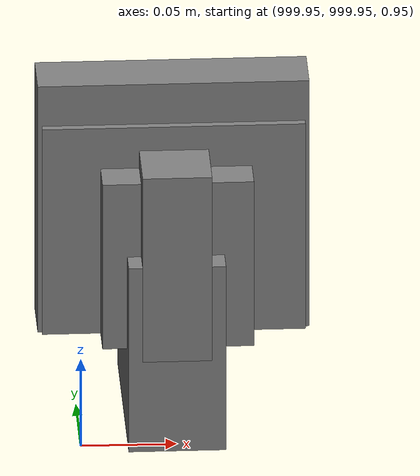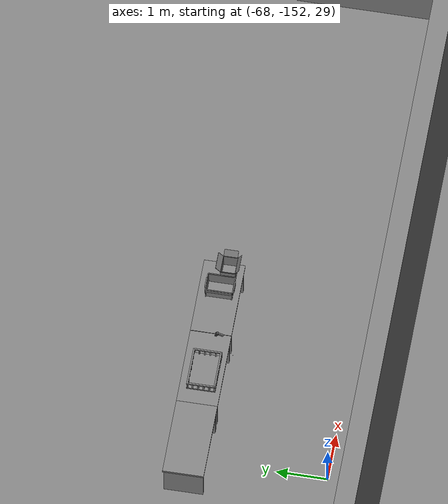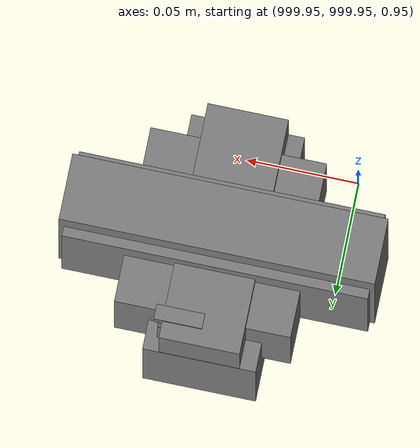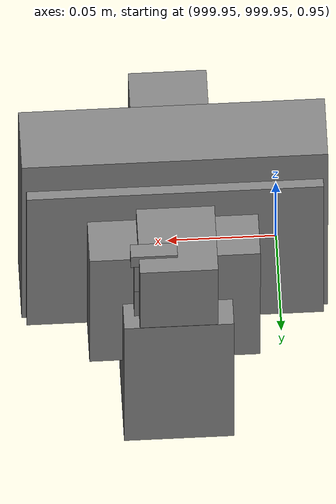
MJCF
<mujoco>
    <option gravity="0.000000000 0.000000000 -9.810000420" timestep="0.0049999999" integrator="implicitfast" density="1.225" viscosity="1.8000001e-05" noslip_iterations="10" iterations="100" sdf_iterations="50">
        <flag multiccd="disable"/>
    </option>
    <size memory="1000M"/>
    <compiler coordinate="local"/>
    <worldbody>
        <light cutoff="30" pos="0 1 1" dir="0 -1 -2"/>
        <light cutoff="30" pos="0 -1 1" dir="0 1 -2"/>
        <body pos="-66.334709167 -149.695022583 31.171602249" euler="58.735008240 18.857166290 66.277488708" mocap="true" name="spotlight6_SpotLight"/>
        <body pos="-66.064399719 -149.687255859 31.167966843" euler="-20.337429047 44.289413452 179.736724854" mocap="true" name="spotlight2_SpotLight"/>
        <body pos="1000.000000000 1000.000000000 1.000000000" euler="0.000000000 0.000000000 180.000000000" name="openloong_gripper_2f85_fix_base_usda_battery_01">
            <geom contype="1" conaffinity="1" density="1000" type="box" material="" rgba="0.500000000 0.500000000 0.500000000 1.000000000" solimp="0.899999976 0.949999988 0.001000000" friction="1.000000000 0.005000000 0.000100000" solref="0.020000000 1.000000000" margin="0" condim="3" group="0" pos="-0.011123657 -0.041940309 0.101691343" quat="1.000000000 0.000000000 0.000000000 0.000000000" size="0.010800000 0.003375000 0.004725000" name="openloong_gripper_2f85_fix_base_usda_geom_8466EBF3_C772_41C4_A7E0_BDF0A98AAA22"/>
            <geom contype="1" conaffinity="1" density="1000" type="box" material="" rgba="0.500000000 0.500000000 0.500000000 1.000000000" solimp="0.899999976 0.949999988 0.001000000" friction="1.000000000 0.005000000 0.000100000" solref="0.020000000 1.000000000" margin="0" condim="3" group="0" pos="-0.010876465 -0.044247437 0.047066893" quat="0.998702705 -0.050920475 0.000000000 0.000000000" size="0.009450001 0.002700000 0.024975000" name="openloong_gripper_2f85_fix_base_usda_geom_A85785A7_67F2_401D_A14F_065181409348"/>
            <geom contype="1" conaffinity="1" density="1000" type="box" material="" rgba="0.500000000 0.500000000 0.500000000 1.000000000" solimp="0.899999976 0.949999988 0.001000000" friction="1.000000000 0.005000000 0.000100000" solref="0.020000000 1.000000000" margin="0" condim="3" group="0" pos="-0.001235962 -0.000659180 0.047381196" quat="1.000000000 0.000000000 0.000000000 0.000000000" size="0.039420001 0.039150000 0.047250003" name="openloong_gripper_2f85_fix_base_usda_geom_29C1EB40_732F_4965_A62A_3268A432F8D0"/>
            <geom contype="1" conaffinity="1" density="1000" type="box" material="" rgba="0.500000000 0.500000000 0.500000000 1.000000000" solimp="0.899999976 0.949999988 0.001000000" friction="1.000000000 0.005000000 0.000100000" solref="0.020000000 1.000000000" margin="0" condim="3" group="0" pos="-0.010876465 -0.039138794 0.009851727" quat="1.000000000 0.000000000 0.000000000 0.000000000" size="0.009450001 0.010800000 0.013500000" name="openloong_gripper_2f85_fix_base_usda_geom_0D292067_547F_4204_BE76_A08A252D2020"/>
            <geom contype="1" conaffinity="1" density="1000" type="box" material="" rgba="0.500000000 0.500000000 0.500000000 1.000000000" solimp="0.899999976 0.949999988 0.001000000" friction="1.000000000 0.005000000 0.000100000" solref="0.020000000 1.000000000" margin="0" condim="3" group="0" pos="-0.010876465 -0.041528322 0.071508206" quat="1.000000000 0.000000000 0.000000000 0.000000000" size="0.009450001 0.002700000 0.027000001" name="openloong_gripper_2f85_fix_base_usda_geom_107A2469_EBB5_481F_8BBD_7F674B699FCB"/>
            <freejoint name="openloong_gripper_2f85_fix_base_usda_battery_01_joint"/>
            <site size="0.005000000 0.005000000 0.005000000" rgba="0.500000000 0.500000000 0.500000000 1.000000000" pos="0.000000000 0.000000000 0.000000000" quat="0.999961913 0.008726500 0.000000000 0.000000000" group="0" type="sphere" name="openloong_gripper_2f85_fix_base_usda_battery_01site"/>
        </body>
        <body pos="1000.000000000 1000.000000000 1.000000000" euler="0.000000000 0.000000000 180.000000000" name="openloong_gripper_2f85_fix_base_usda_cpu_fan">
            <geom contype="1" conaffinity="1" density="1000" type="box" material="" rgba="0.500000000 0.500000000 0.500000000 1.000000000" solimp="0.899999976 0.949999988 0.001000000" friction="1.000000000 0.005000000 0.000100000" solref="0.020000000 1.000000000" margin="0" condim="3" group="0" pos="0.000000000 0.000000000 0.070034981" quat="0.000000000 0.000000000 0.000000000 1.000000000" size="0.070700005 0.014699999 0.070700005" name="openloong_gripper_2f85_fix_base_usda_geom_1562DE64_DC5E_44E2_82CE_D125C5FB91B0"/>
            <freejoint name="openloong_gripper_2f85_fix_base_usda_cpu_fan_joint"/>
            <site size="0.005000000 0.005000000 0.005000000" rgba="0.500000000 0.500000000 0.500000000 1.000000000" pos="0.000000000 0.000000000 0.000000000" quat="0.999961913 0.008726535 0.000000000 0.000000000" group="0" type="sphere" name="openloong_gripper_2f85_fix_base_usda_cpu_fancsite"/>
        </body>
        <body pos="1000.000000000 1000.000000000 1.000000000" euler="0.000011953 0.000005123 -179.999984741" name="openloong_gripper_2f85_fix_base_usda_intel_box">
            <geom contype="1" conaffinity="1" density="1000" type="box" material="" rgba="0.500000000 0.500000000 0.500000000 1.000000000" solimp="0.899999976 0.949999988 0.001000000" friction="1.000000000 0.005000000 0.000100000" solref="0.020000000 1.000000000" margin="0" condim="3" group="0" pos="0.000000000 -0.000067139 0.000082284" quat="0.707106709 0.000000225 0.000000253 0.707106650" size="0.052800003 0.025300000 0.052800003" name="openloong_gripper_2f85_fix_base_usda_geom_6A7EC48A_1E1A_43C6_9C86_824824E62075"/>
            <freejoint name="openloong_gripper_2f85_fix_base_usda_intel_box_joint"/>
            <site size="0.005000000 0.005000000 0.005000000" rgba="0.500000000 0.500000000 0.500000000 1.000000000" pos="0.000000000 0.000000000 0.000000000" quat="0.999961913 0.008726500 0.000000000 0.000000000" group="0" type="sphere" name="openloong_gripper_2f85_fix_base_usda_intel_boxsite"/>
        </body>
        <body pos="1000.000000000 1000.000000000 1.000000000" euler="0.000000000 0.000000000 180.000000000" name="openloong_gripper_2f85_fix_base_usda_wifi_box">
            <geom contype="1" conaffinity="1" density="1000" type="box" material="" rgba="0.500000000 0.500000000 0.500000000 1.000000000" solimp="0.899999976 0.949999988 0.001000000" friction="1.000000000 0.005000000 0.000100000" solref="0.020000000 1.000000000" margin="0" condim="3" group="0" pos="0.000000000 0.000000000 0.058978677" quat="0.000000000 0.000000047 0.000000000 1.000000000" size="0.068499997 0.018999999 0.059000000" name="openloong_gripper_2f85_fix_base_usda_geom_3AD4041B_1AA8_4FD3_B788_41722BF4B6C9"/>
            <freejoint name="openloong_gripper_2f85_fix_base_usda_wifi_box_joint"/>
            <site size="0.005000000 0.005000000 0.005000000" rgba="0.500000000 0.500000000 0.500000000 1.000000000" pos="0.000000000 0.000000000 0.000000000" quat="0.999961913 0.008726500 0.000000000 0.000000000" group="0" type="sphere" name="openloong_gripper_2f85_fix_base_usda_wifi_boxsite"/>
        </body>
        <body pos="-65.984939575 -148.941268921 31.168954849" euler="84.528099060 -37.020790100 -154.916336060" mocap="true" name="spotlight5_SpotLight"/>
        <body pos="1000.000000000 999.999938965 1.000000000" euler="0.000000000 0.000000000 180.000000000" name="openloong_gripper_2f85_fix_base_usda_intelcore_i5">
            <geom contype="1" conaffinity="1" density="1000" type="box" material="" rgba="0.500000000 0.500000000 0.500000000 1.000000000" solimp="0.899999976 0.949999988 0.001000000" friction="1.000000000 0.005000000 0.000100000" solref="0.020000000 1.000000000" margin="0" condim="3" group="0" pos="0.000000000 0.000000000 0.051722717" quat="0.707106709 0.000000000 0.000000000 -0.707106769" size="0.052800000 0.018080002 0.052800000" name="openloong_gripper_2f85_fix_base_usda_geom_03071380_3A2E_4A90_A960_5822AD2BC62B"/>
            <freejoint name="openloong_gripper_2f85_fix_base_usda_intelcore_i5_joint"/>
            <site size="0.005000000 0.005000000 0.005000000" rgba="0.500000000 0.500000000 0.500000000 1.000000000" pos="0.000000000 0.000000000 0.000000000" quat="0.999961913 0.008726534 0.000000000 0.000000000" group="0" type="sphere" name="openloong_gripper_2f85_fix_base_usda_intelcore_i5site"/>
        </body>
        <body pos="-64.866622925 -149.383972168 30.183746338" euler="89.999984741 89.999946594 0.000000000" name="openloong_gripper_2f85_fix_base_usda_bluebox_01">
            <geom contype="1" conaffinity="1" density="1000" type="box" material="" rgba="0.500000000 0.500000000 0.500000000 1.000000000" solimp="0.899999976 0.949999988 0.001000000" friction="1.000000000 0.005000000 0.000100000" solref="0.020000000 1.000000000" margin="0" condim="3" group="0" pos="0.276580811 0.187225342 0.000068665" quat="0.707106948 0.000077471 0.707106352 0.000077486" size="0.100000001 0.057999998 0.010000000" name="openloong_gripper_2f85_fix_base_usda_geom_EFCE1E25_FF10_452D_AC14_F2580D48A57E"/>
            <geom contype="1" conaffinity="1" density="1000" type="box" material="" rgba="0.500000000 0.500000000 0.500000000 1.000000000" solimp="0.899999976 0.949999988 0.001000000" friction="1.000000000 0.005000000 0.000100000" solref="0.020000000 1.000000000" margin="0" condim="3" group="0" pos="0.000000000 0.002883911 0.000000000" quat="0.999999881 0.000000000 0.000000000 0.000000000" size="0.254000008 0.003000000 0.172000006" name="openloong_gripper_2f85_fix_base_usda_geom_8D4F5BE3_B152_4207_862A_28BE251B16C5"/>
            <geom contype="1" conaffinity="1" density="1000" type="box" material="" rgba="0.500000000 0.500000000 0.500000000 1.000000000" solimp="0.899999976 0.949999988 0.001000000" friction="1.000000000 0.005000000 0.000100000" solref="0.020000000 1.000000000" margin="0" condim="3" group="0" pos="0.000000000 0.124874115 0.173484802" quat="0.999796331 0.020176515 -0.000000015 0.000000030" size="0.259999990 0.119999997 0.007000000" name="openloong_gripper_2f85_fix_base_usda_geom_9F5BCDC1_9DF2_42C1_8148_B6AE6DE8E0DB"/>
            <geom contype="1" conaffinity="1" density="1000" type="box" material="" rgba="0.500000000 0.500000000 0.500000000 1.000000000" solimp="0.899999976 0.949999988 0.001000000" friction="1.000000000 0.005000000 0.000100000" solref="0.020000000 1.000000000" margin="0" condim="3" group="0" pos="0.000000000 0.124874115 -0.173469543" quat="0.999796331 -0.020176545 -0.000000015 0.000000000" size="0.259999990 0.119999997 0.007000000" name="openloong_gripper_2f85_fix_base_usda_geom_D474C275_9E21_45EE_95B8_33EFC4D07EE7"/>
            <geom contype="1" conaffinity="1" density="1000" type="box" material="" rgba="0.500000000 0.500000000 0.500000000 1.000000000" solimp="0.899999976 0.949999988 0.001000000" friction="1.000000000 0.005000000 0.000100000" solref="0.020000000 1.000000000" margin="0" condim="3" group="0" pos="0.000000000 0.214008331 0.188980103" quat="0.999912977 0.013176724 0.000000015 0.000000000" size="0.259999990 0.029999999 0.012500000" name="openloong_gripper_2f85_fix_base_usda_geom_80ED4E0A_61F8_4DFA_A0E4_2D405D7331B2"/>
            <geom contype="1" conaffinity="1" density="1000" type="box" material="" rgba="0.500000000 0.500000000 0.500000000 1.000000000" solimp="0.899999976 0.949999988 0.001000000" friction="1.000000000 0.005000000 0.000100000" solref="0.020000000 1.000000000" margin="0" condim="3" group="0" pos="-0.258361816 0.125289917 0.001876831" quat="0.702796936 -0.020792112 0.710783124 0.020769298" size="0.189999998 0.119999997 0.009000000" name="openloong_gripper_2f85_fix_base_usda_geom_22B23619_EE0D_4D66_A7A0_D8E427AFCE3D"/>
            <geom contype="1" conaffinity="1" density="1000" type="box" material="" rgba="0.500000000 0.500000000 0.500000000 1.000000000" solimp="0.899999976 0.949999988 0.001000000" friction="1.000000000 0.005000000 0.000100000" solref="0.020000000 1.000000000" margin="0" condim="3" group="0" pos="0.000000000 0.214008331 -0.188980103" quat="0.999912977 -0.013176769 0.000000030 0.000000015" size="0.259999990 0.029999999 0.012500000" name="openloong_gripper_2f85_fix_base_usda_geom_BB16DDAB_E1F8_4E03_9292_80784B1BB389"/>
            <geom contype="1" conaffinity="1" density="1000" type="box" material="" rgba="0.500000000 0.500000000 0.500000000 1.000000000" solimp="0.899999976 0.949999988 0.001000000" friction="1.000000000 0.005000000 0.000100000" solref="0.020000000 1.000000000" margin="0" condim="3" group="0" pos="-0.276611328 0.187225342 0.000068665" quat="0.707106650 0.000077441 0.707106709 0.000077456" size="0.100000001 0.057999998 0.010000000" name="openloong_gripper_2f85_fix_base_usda_geom_3D5DDDFA_A805_4116_92AE_71C8F50BC50F"/>
            <geom contype="1" conaffinity="1" density="1000" type="box" material="" rgba="0.500000000 0.500000000 0.500000000 1.000000000" solimp="0.899999976 0.949999988 0.001000000" friction="1.000000000 0.005000000 0.000100000" solref="0.020000000 1.000000000" margin="0" condim="3" group="0" pos="0.258331299 0.125289917 0.001876831" quat="0.702851415 0.018856421 0.710823774 -0.019329369" size="0.189999998 0.119999997 0.009000000" name="openloong_gripper_2f85_fix_base_usda_geom_04E129FA_4E16_49CC_BDA0_0C30B28A0E30"/>
            <freejoint name="openloong_gripper_2f85_fix_base_usda_bluebox_01_joint"/>
            <site size="0.005000000 0.005000000 0.005000000" rgba="0.500000000 0.500000000 0.500000000 1.000000000" pos="0.000000000 0.000000000 0.000000000" quat="0.999961913 0.008726534 0.000000000 0.000000000" group="0" type="sphere" name="openloong_gripper_2f85_fix_base_usda_bluebox_01site"/>
        </body>
        <body pos="-64.496299744 -149.491867065 30.235729218" euler="0.000000000 0.000000000 89.999946594" name="openloong_gripper_2f85_fix_base_usda_cardboardbox_01">
            <geom contype="1" conaffinity="1" density="1000" type="box" material="" rgba="0.500000000 0.500000000 0.500000000 1.000000000" solimp="0.899999976 0.949999988 0.001000000" friction="1.000000000 0.005000000 0.000100000" solref="0.020000000 1.000000000" margin="0" condim="3" group="0" pos="-0.003166199 -0.004086494 0.005052090" quat="1.000000000 0.000000000 0.000000000 0.000000000" size="0.142499998 0.177500010 0.005000000" name="openloong_gripper_2f85_fix_base_usda_geom_EE20DFEA_8F04_4EFD_86F2_273D147DDACE"/>
            <geom contype="1" conaffinity="1" density="1000" type="box" material="" rgba="0.500000000 0.500000000 0.500000000 1.000000000" solimp="0.899999976 0.949999988 0.001000000" friction="1.000000000 0.005000000 0.000100000" solref="0.020000000 1.000000000" margin="0" condim="3" group="0" pos="-0.003166199 0.170316696 0.150570869" quat="1.000000000 0.000000000 0.000000000 0.000000000" size="0.142499998 0.005000000 0.149999991" name="openloong_gripper_2f85_fix_base_usda_geom_0BDA82F8_4659_419B_8B98_A3F4D1705B37"/>
            <geom contype="1" conaffinity="1" density="1000" type="box" material="" rgba="0.500000000 0.500000000 0.500000000 1.000000000" solimp="0.899999976 0.949999988 0.001000000" friction="1.000000000 0.005000000 0.000100000" solref="0.020000000 1.000000000" margin="0" condim="3" group="0" pos="-0.147399902 -0.005307198 0.150570869" quat="1.000000000 0.000000000 0.000000000 0.000000000" size="0.005000000 0.177500010 0.149999991" name="openloong_gripper_2f85_fix_base_usda_geom_C7F4ABFD_C8AB_4130_BB3E_076D0DC83BB1"/>
            <geom contype="1" conaffinity="1" density="1000" type="box" material="" rgba="0.500000000 0.500000000 0.500000000 1.000000000" solimp="0.899999976 0.949999988 0.001000000" friction="1.000000000 0.005000000 0.000100000" solref="0.020000000 1.000000000" margin="0" condim="3" group="0" pos="0.140275955 -0.005307198 0.150570869" quat="1.000000000 0.000000000 0.000000000 0.000000000" size="0.005000000 0.177500010 0.149999991" name="openloong_gripper_2f85_fix_base_usda_geom_247AEECC_B866_484A_B3A9_D7FAD97F0BB6"/>
            <geom contype="1" conaffinity="1" density="1000" type="box" material="" rgba="0.500000000 0.500000000 0.500000000 1.000000000" solimp="0.899999976 0.949999988 0.001000000" friction="1.000000000 0.005000000 0.000100000" solref="0.020000000 1.000000000" margin="0" condim="3" group="0" pos="-0.003166199 -0.181550980 0.150570869" quat="1.000000000 0.000000000 0.000000000 0.000000000" size="0.142499998 0.005000000 0.149999991" name="openloong_gripper_2f85_fix_base_usda_geom_3625CB43_0831_4548_B5E2_2F6467C5803B"/>
            <freejoint name="openloong_gripper_2f85_fix_base_usda_cardboardbox_01_joint"/>
            <site size="0.005000000 0.005000000 0.005000000" rgba="0.500000000 0.500000000 0.500000000 1.000000000" pos="0.000000000 0.000000000 0.000000000" quat="0.999961913 0.008726535 0.000000000 0.000000000" group="0" type="sphere" name="openloong_gripper_2f85_fix_base_usda_site_F4EF1CA3_BD3C_4C81_A807_5B2C9D9E3926"/>
            <body pos="0.139160156 -0.004048347 0.301930904" euler="-179.999954224 49.383502960 179.999954224" name="openloong_gripper_2f85_fix_base_usda_A1_006">
                <geom contype="1" conaffinity="1" density="1000" type="box" material="" rgba="0.500000000 0.500000000 0.500000000 1.000000000" solimp="0.899999976 0.949999988 0.001000000" friction="1.000000000 0.005000000 0.000100000" solref="0.020000000 1.000000000" margin="0" condim="3" group="0" pos="-0.071587563 0.000009537 0.001745224" quat="0.999999881 0.000000000 0.000000000 0.000000000" size="0.071249999 0.179999992 0.002500000" name="openloong_gripper_2f85_fix_base_usda_geom_2E63B3D8_E364_45A7_8CFE_9C699A098BD8"/>
                <joint armature="0" stiffness="0.07" damping="0.0099999998" axis="0.000000 1.000000 0.000000" type="hinge" name="openloong_gripper_2f85_fix_base_usda_A1_006"/>
            </body>
            <body pos="-0.145902634 -0.004086494 0.301938057" euler="-180.000000000 -60.000011444 -180.000000000" name="openloong_gripper_2f85_fix_base_usda_A2_006">
                <geom contype="1" conaffinity="1" density="1000" type="box" material="" rgba="0.500000000 0.500000000 0.500000000 1.000000000" solimp="0.899999976 0.949999988 0.001000000" friction="1.000000000 0.005000000 0.000100000" solref="0.020000000 1.000000000" margin="0" condim="3" group="0" pos="0.071268082 0.000009537 0.002717972" quat="0.000002921 0.000000000 -0.000000030 0.999999881" size="0.071249999 0.179999992 0.002500000" name="openloong_gripper_2f85_fix_base_usda_geom_6D7E8618_EEC8_47CD_81E8_744A8659E525"/>
                <joint armature="0" stiffness="0.07" damping="0.0099999998" axis="0.000000 1.000000 0.000000" type="hinge" name="openloong_gripper_2f85_fix_base_usda_A2_006"/>
            </body>
            <body pos="-0.003385544 0.175991058 0.301930904" euler="-125.858116150 -0.000004561 0.000002331" name="openloong_gripper_2f85_fix_base_usda_B2_006">
                <geom contype="1" conaffinity="1" density="1000" type="box" material="" rgba="0.500000000 0.500000000 0.500000000 1.000000000" solimp="0.899999976 0.949999988 0.001000000" friction="1.000000000 0.005000000 0.000100000" solref="0.020000000 1.000000000" margin="0" condim="3" group="0" pos="0.000009537 -0.070939064 -0.002470016" quat="0.999614120 0.027776197 -0.000000015 0.000000030" size="0.137500003 0.064999998 0.005000000" name="openloong_gripper_2f85_fix_base_usda_geom_1128B670_22F1_4899_B214_968D5E8640BE"/>
                <joint armature="0" stiffness="0.07" damping="0.0099999998" axis="1.000000 0.000000 0.000000" type="hinge" name="openloong_gripper_2f85_fix_base_usda_B2_006"/>
            </body>
            <body pos="-0.003385544 -0.184140205 0.301938057" euler="147.805557251 0.000000000 0.000000000" name="openloong_gripper_2f85_fix_base_usda_B1_006">
                <geom contype="1" conaffinity="1" density="1000" type="box" material="" rgba="0.500000000 0.500000000 0.500000000 1.000000000" solimp="0.899999976 0.949999988 0.001000000" friction="1.000000000 0.005000000 0.000100000" solref="0.020000000 1.000000000" margin="0" condim="3" group="0" pos="-0.000028610 0.070202351 -0.002703667" quat="0.999614179 -0.027776167 0.000000000 0.000000000" size="0.137500003 0.064999998 0.005000000" name="openloong_gripper_2f85_fix_base_usda_geom_754792B8_5D25_4C05_B164_2FEF17B99C86"/>
                <joint armature="0" stiffness="0.07" damping="0.0099999998" axis="1.000000 0.000000 0.000000" type="hinge" name="openloong_gripper_2f85_fix_base_usda_B1_006"/>
            </body>
        </body>
        <body pos="-65.882858276 -149.481979370 30.229999542" euler="-64.487716675 0.000000000 0.000000000" name="openloong_gripper_2f85_fix_base_usda_Barcode">
            <geom contype="1" conaffinity="1" density="1000" type="box" material="" rgba="0.500000000 0.500000000 0.500000000 1.000000000" solimp="0.899999976 0.949999988 0.001000000" friction="1.000000000 0.005000000 0.000100000" solref="0.020000000 1.000000000" margin="0" condim="3" group="0" pos="0.000000000 0.013038635 0.001419067" quat="0.000000000 0.000000000 0.000000000 1.000000119" size="0.034000002 0.010000000 0.017999999" name="openloong_gripper_2f85_fix_base_usda_geom_255F3D60_DDF9_46E2_AAFD_E2892C0AFCEB"/>
            <geom contype="1" conaffinity="1" density="1000" type="box" material="" rgba="0.500000000 0.500000000 0.500000000 1.000000000" solimp="0.899999976 0.949999988 0.001000000" friction="1.000000000 0.005000000 0.000100000" solref="0.020000000 1.000000000" margin="0" condim="3" group="0" pos="0.000000000 -0.035301208 -0.007095337" quat="0.000000000 0.000000000 -0.043619365 0.999048233" size="0.028999999 0.010000000 0.020000000" name="openloong_gripper_2f85_fix_base_usda_geom_D0CE950E_E545_4419_AEB7_A31398C623F6"/>
            <geom contype="1" conaffinity="1" density="1000" type="box" material="" rgba="0.500000000 0.500000000 0.500000000 1.000000000" solimp="0.899999976 0.949999988 0.001000000" friction="1.000000000 0.005000000 0.000100000" solref="0.020000000 1.000000000" margin="0" condim="3" group="0" pos="0.000000000 -0.043411255 -0.011749268" quat="0.922262907 0.386563420 0.000000000 0.000000000" size="0.026000001 0.010000000 0.020000000" name="openloong_gripper_2f85_fix_base_usda_geom_D4E7B683_54D1_45A6_AB20_794BD67F852E"/>
            <geom contype="1" conaffinity="1" density="1000" type="box" material="" rgba="0.500000000 0.500000000 0.500000000 1.000000000" solimp="0.899999976 0.949999988 0.001000000" friction="1.000000000 0.005000000 0.000100000" solref="0.020000000 1.000000000" margin="0" condim="3" group="0" pos="0.000000000 -0.016967773 -0.031860352" quat="0.000000000 0.000000000 0.000000000 1.000000119" size="0.008000000 0.010000000 0.013000000" name="openloong_gripper_2f85_fix_base_usda_geom_E83E5A1D_9B48_440E_931F_1145ECA7FF92"/>
            <geom contype="1" conaffinity="1" density="1000" type="box" material="" rgba="0.500000000 0.500000000 0.500000000 1.000000000" solimp="0.899999976 0.949999988 0.001000000" friction="1.000000000 0.005000000 0.000100000" solref="0.020000000 1.000000000" margin="0" condim="3" group="0" pos="0.000000000 -0.001869202 0.000312805" quat="0.953716993 0.300705761 0.000000000 0.000000000" size="0.032000002 0.010000000 0.018999999" name="openloong_gripper_2f85_fix_base_usda_geom_BD478574_8F67_423D_B46F_DBFF0B9AA02A"/>
            <geom contype="1" conaffinity="1" density="1000" type="box" material="" rgba="0.500000000 0.500000000 0.500000000 1.000000000" solimp="0.899999976 0.949999988 0.001000000" friction="1.000000000 0.005000000 0.000100000" solref="0.020000000 1.000000000" margin="0" condim="3" group="0" pos="0.000000000 -0.019531250 -0.003173828" quat="0.953716993 0.300705761 0.000000000 0.000000000" size="0.030999999 0.010000000 0.020000000" name="openloong_gripper_2f85_fix_base_usda_geom_B1ED35C4_1230_4F4E_A7A8_BCA6B746F186"/>
            <geom contype="1" conaffinity="1" density="1000" type="box" material="" rgba="0.500000000 0.500000000 0.500000000 1.000000000" solimp="0.899999976 0.949999988 0.001000000" friction="1.000000000 0.005000000 0.000100000" solref="0.020000000 1.000000000" margin="0" condim="3" group="0" pos="0.000000000 -0.035301208 -0.007095337" quat="0.953716993 0.300705761 0.000000000 0.000000000" size="0.028999999 0.010000000 0.020000000" name="openloong_gripper_2f85_fix_base_usda_geom_BA7C5D9C_3B82_48A3_954B_95A878A67615"/>
            <geom contype="1" conaffinity="1" density="1000" type="box" material="" rgba="0.500000000 0.500000000 0.500000000 1.000000000" solimp="0.899999976 0.949999988 0.001000000" friction="1.000000000 0.005000000 0.000100000" solref="0.020000000 1.000000000" margin="0" condim="3" group="0" pos="0.000000000 -0.042617798 -0.071121216" quat="0.000000000 0.000000000 0.000000000 1.000000119" size="0.013000000 0.021000000 0.059999999" name="openloong_gripper_2f85_fix_base_usda_geom_0F7B245B_3708_4F7E_ABE2_84F47CCBD379"/>
            <freejoint name="openloong_gripper_2f85_fix_base_usda_Barcode_joint"/>
            <site size="0.005000000 0.005000000 0.005000000" rgba="0.500000000 0.500000000 0.500000000 1.000000000" pos="0.000000000 0.000000000 0.000000000" quat="1.000000000 0.000000000 0.000000000 0.000000000" group="0" type="sphere" name="openloong_gripper_2f85_fix_base_usda_Barcode_site"/>
        </body>
        <body pos="-66.745018005 -149.392349243 30.184000015" euler="0.000000000 0.000000000 89.999946594" name="[22330142614684]_Basket_01">
            <geom contype="1" conaffinity="1" density="1000" type="box" material="" rgba="0.500000000 0.500000000 0.500000000 1.000000000" solimp="0.899999976 0.949999988 0.001000000" friction="1.000000000 0.005000000 0.000100000" solref="0.020000000 1.000000000" margin="0" condim="3" group="0" pos="-0.052425385 0.389207840 0.089787483" quat="0.707107008 0.000000000 0.000000000 0.707106411" size="0.014249999 0.014249999 0.059999999" name="[22330142614684]_geom_034140E6_B5B4_4F1C_9E89_136DDBC4996C"/>
            <geom contype="1" conaffinity="1" density="1000" type="box" material="" rgba="0.500000000 0.500000000 0.500000000 1.000000000" solimp="0.899999976 0.949999988 0.001000000" friction="1.000000000 0.005000000 0.000100000" solref="0.020000000 1.000000000" margin="0" condim="3" group="0" pos="0.264015198 -0.133043289 0.089787483" quat="0.707107008 0.000000000 0.000000000 0.707106411" size="0.014249999 0.014249999 0.059999999" name="[22330142614684]_geom_C309148C_2DF9_4505_9355_487899163868"/>
            <geom contype="1" conaffinity="1" density="1000" type="box" material="" rgba="0.500000000 0.500000000 0.500000000 1.000000000" solimp="0.899999976 0.949999988 0.001000000" friction="1.000000000 0.005000000 0.000100000" solref="0.020000000 1.000000000" margin="0" condim="3" group="0" pos="-0.264015198 -0.265548706 0.089793205" quat="0.707107008 0.000000000 0.000000000 0.707106411" size="0.014249999 0.014249999 0.059999999" name="[22330142614684]_geom_2A15B9CA_C70E_471F_971E_4C5B49223AFA"/>
            <geom contype="1" conaffinity="1" density="1000" type="box" material="" rgba="0.500000000 0.500000000 0.500000000 1.000000000" solimp="0.899999976 0.949999988 0.001000000" friction="1.000000000 0.005000000 0.000100000" solref="0.020000000 1.000000000" margin="0" condim="3" group="0" pos="-0.160263062 -0.389322281 0.089793205" quat="0.707107008 0.000000000 0.000000000 0.707106411" size="0.014249999 0.014249999 0.059999999" name="[22330142614684]_geom_D4FD36DD_0EFB_457D_ACD5_324DE49A35EA"/>
            <geom contype="1" conaffinity="1" density="1000" type="box" material="" rgba="0.500000000 0.500000000 0.500000000 1.000000000" solimp="0.899999976 0.949999988 0.001000000" friction="1.000000000 0.005000000 0.000100000" solref="0.020000000 1.000000000" margin="0" condim="3" group="0" pos="0.162265778 -0.389322281 0.089787483" quat="0.707107008 0.000000000 0.000000000 0.707106411" size="0.014249999 0.014249999 0.059999999" name="[22330142614684]_geom_F7D6D6BC_B1F2_46A0_AFDC_03D0CE834064"/>
            <geom contype="1" conaffinity="1" density="1000" type="box" material="" rgba="0.500000000 0.500000000 0.500000000 1.000000000" solimp="0.899999976 0.949999988 0.001000000" friction="1.000000000 0.005000000 0.000100000" solref="0.020000000 1.000000000" margin="0" condim="3" group="0" pos="0.264015198 0.389207840 0.089787483" quat="0.707107008 0.000000000 0.000000000 0.707106411" size="0.014249999 0.014249999 0.059999999" name="[22330142614684]_geom_0FF9F005_D213_489A_85B2_E31060A18BB0"/>
            <geom contype="1" conaffinity="1" density="1000" type="box" material="" rgba="0.500000000 0.500000000 0.500000000 1.000000000" solimp="0.899999976 0.949999988 0.001000000" friction="1.000000000 0.005000000 0.000100000" solref="0.020000000 1.000000000" margin="0" condim="3" group="0" pos="-0.264015198 -0.133043289 0.089793205" quat="0.707107008 0.000000000 0.000000000 0.707106411" size="0.014249999 0.014249999 0.059999999" name="[22330142614684]_geom_8C3A18D4_D755_48BE_8CB0_4488F1B8B0EE"/>
            <geom contype="1" conaffinity="1" density="1000" type="box" material="" rgba="0.500000000 0.500000000 0.500000000 1.000000000" solimp="0.899999976 0.949999988 0.001000000" friction="1.000000000 0.005000000 0.000100000" solref="0.020000000 1.000000000" margin="0" condim="3" group="0" pos="-0.264026642 0.269256592 0.089793205" quat="0.707107008 0.000000000 0.000000000 0.707106411" size="0.014249999 0.014249999 0.059999999" name="[22330142614684]_geom_47FB4D08_0A80_4937_A73A_117F69C05077"/>
            <geom contype="1" conaffinity="1" density="1000" type="box" material="" rgba="0.500000000 0.500000000 0.500000000 1.000000000" solimp="0.899999976 0.949999988 0.001000000" friction="1.000000000 0.005000000 0.000100000" solref="0.020000000 1.000000000" margin="0" condim="3" group="0" pos="0.054462433 0.389207840 0.089787483" quat="0.707107008 0.000000000 0.000000000 0.707106411" size="0.014249999 0.014249999 0.059999999" name="[22330142614684]_geom_1A98B285_F20B_4E60_9B05_C6C21FCFC000"/>
            <geom contype="1" conaffinity="1" density="1000" type="box" material="" rgba="0.500000000 0.500000000 0.500000000 1.000000000" solimp="0.899999976 0.949999988 0.001000000" friction="1.000000000 0.005000000 0.000100000" solref="0.020000000 1.000000000" margin="0" condim="3" group="0" pos="0.054462433 -0.389322281 0.089787483" quat="0.707107008 0.000000000 0.000000000 0.707106411" size="0.014249999 0.014249999 0.059999999" name="[22330142614684]_geom_1EE79B31_99F8_4CD0_9570_BBA04520636A"/>
            <geom contype="1" conaffinity="1" density="1000" type="box" material="" rgba="0.500000000 0.500000000 0.500000000 1.000000000" solimp="0.899999976 0.949999988 0.001000000" friction="1.000000000 0.005000000 0.000100000" solref="0.020000000 1.000000000" margin="0" condim="3" group="0" pos="0.264015198 0.269256592 0.089793205" quat="0.707107008 0.000000000 0.000000000 0.707106411" size="0.014249999 0.014249999 0.059999999" name="[22330142614684]_geom_66800CBB_8675_40EB_B616_33448644599F"/>
            <geom contype="1" conaffinity="1" density="1000" type="box" material="" rgba="0.500000000 0.500000000 0.500000000 1.000000000" solimp="0.899999976 0.949999988 0.001000000" friction="1.000000000 0.005000000 0.000100000" solref="0.020000000 1.000000000" margin="0" condim="3" group="0" pos="0.264015198 -0.389322281 0.089787483" quat="0.707107008 0.000000000 0.000000000 0.707106411" size="0.014249999 0.014249999 0.059999999" name="[22330142614684]_geom_D7BA5609_43E3_4DBC_9AD5_CF56F9A3CB52"/>
            <geom contype="1" conaffinity="1" density="1000" type="box" material="" rgba="0.500000000 0.500000000 0.500000000 1.000000000" solimp="0.899999976 0.949999988 0.001000000" friction="1.000000000 0.005000000 0.000100000" solref="0.020000000 1.000000000" margin="0" condim="3" group="0" pos="0.000000000 0.000000000 0.015998840" quat="0.707107008 0.000000000 0.000000000 0.707106411" size="0.403499991 0.279000014 0.015750000" name="[22330142614684]_geom_1A4BA243_30E1_4DDB_9FA2_D6D763CE84D1"/>
            <geom contype="1" conaffinity="1" density="1000" type="box" material="" rgba="0.500000000 0.500000000 0.500000000 1.000000000" solimp="0.899999976 0.949999988 0.001000000" friction="1.000000000 0.005000000 0.000100000" solref="0.020000000 1.000000000" margin="0" condim="3" group="0" pos="0.000000000 -0.389476776 0.163619041" quat="0.707107008 0.000000000 0.000000000 0.707106411" size="0.015000000 0.277500004 0.015750000" name="[22330142614684]_geom_3E07F6A1_C76D_4279_A277_84D35C6E6D01"/>
            <geom contype="1" conaffinity="1" density="1000" type="box" material="" rgba="0.500000000 0.500000000 0.500000000 1.000000000" solimp="0.899999976 0.949999988 0.001000000" friction="1.000000000 0.005000000 0.000100000" solref="0.020000000 1.000000000" margin="0" condim="3" group="0" pos="0.162265778 0.389207840 0.089787483" quat="0.707107008 0.000000000 0.000000000 0.707106411" size="0.014249999 0.014249999 0.059999999" name="[22330142614684]_geom_330E424F_B83D_4136_86B8_5883DA6364CB"/>
            <geom contype="1" conaffinity="1" density="1000" type="box" material="" rgba="0.500000000 0.500000000 0.500000000 1.000000000" solimp="0.899999976 0.949999988 0.001000000" friction="1.000000000 0.005000000 0.000100000" solref="0.020000000 1.000000000" margin="0" condim="3" group="0" pos="0.000000000 0.389471054 0.163619041" quat="0.707107008 0.000000000 0.000000000 0.707106411" size="0.015000000 0.277500004 0.015750000" name="[22330142614684]_geom_3B530259_FCDE_479D_B924_8A681061C38D"/>
            <geom contype="1" conaffinity="1" density="1000" type="box" material="" rgba="0.500000000 0.500000000 0.500000000 1.000000000" solimp="0.899999976 0.949999988 0.001000000" friction="1.000000000 0.005000000 0.000100000" solref="0.020000000 1.000000000" margin="0" condim="3" group="0" pos="-0.263511658 0.000000000 0.163619041" quat="0.707107008 0.000000000 0.000000000 0.707106411" size="0.403499991 0.015000000 0.015750000" name="[22330142614684]_geom_8ECD5DF0_BBC1_48F5_8BE0_292C79C3702B"/>
            <geom contype="1" conaffinity="1" density="1000" type="box" material="" rgba="0.500000000 0.500000000 0.500000000 1.000000000" solimp="0.899999976 0.949999988 0.001000000" friction="1.000000000 0.005000000 0.000100000" solref="0.020000000 1.000000000" margin="0" condim="3" group="0" pos="-0.264015198 0.141334534 0.089793205" quat="0.707107008 0.000000000 0.000000000 0.707106411" size="0.014249999 0.014249999 0.059999999" name="[22330142614684]_geom_0FCA0F16_C7CA_4716_988F_660562263667"/>
            <geom contype="1" conaffinity="1" density="1000" type="box" material="" rgba="0.500000000 0.500000000 0.500000000 1.000000000" solimp="0.899999976 0.949999988 0.001000000" friction="1.000000000 0.005000000 0.000100000" solref="0.020000000 1.000000000" margin="0" condim="3" group="0" pos="0.264015198 -0.265548706 0.089787483" quat="0.707107008 0.000000000 0.000000000 0.707106411" size="0.014249999 0.014249999 0.059999999" name="[22330142614684]_geom_2732AB31_0B2E_4C06_93F0_108EC0987544"/>
            <geom contype="1" conaffinity="1" density="1000" type="box" material="" rgba="0.500000000 0.500000000 0.500000000 1.000000000" solimp="0.899999976 0.949999988 0.001000000" friction="1.000000000 0.005000000 0.000100000" solref="0.020000000 1.000000000" margin="0" condim="3" group="0" pos="-0.160263062 0.389207840 0.089787483" quat="0.707107008 0.000000000 0.000000000 0.707106411" size="0.014249999 0.014249999 0.059999999" name="[22330142614684]_geom_428B8ADC_A66A_4FD4_9748_885F3DC0C35A"/>
            <geom contype="1" conaffinity="1" density="1000" type="box" material="" rgba="0.500000000 0.500000000 0.500000000 1.000000000" solimp="0.899999976 0.949999988 0.001000000" friction="1.000000000 0.005000000 0.000100000" solref="0.020000000 1.000000000" margin="0" condim="3" group="0" pos="-0.052425385 -0.389322281 0.089787483" quat="0.707107008 0.000000000 0.000000000 0.707106411" size="0.014249999 0.014249999 0.059999999" name="[22330142614684]_geom_ECB030D5_5CFF_4475_9E63_0C00E49C6EC4"/>
            <geom contype="1" conaffinity="1" density="1000" type="box" material="" rgba="0.500000000 0.500000000 0.500000000 1.000000000" solimp="0.899999976 0.949999988 0.001000000" friction="1.000000000 0.005000000 0.000100000" solref="0.020000000 1.000000000" margin="0" condim="3" group="0" pos="-0.264026642 -0.389322281 0.089793205" quat="0.707107008 0.000000000 0.000000000 0.707106411" size="0.014249999 0.014249999 0.059999999" name="[22330142614684]_geom_41893E2C_9156_4902_82A6_BDC95DBBB20B"/>
            <geom contype="1" conaffinity="1" density="1000" type="box" material="" rgba="0.500000000 0.500000000 0.500000000 1.000000000" solimp="0.899999976 0.949999988 0.001000000" friction="1.000000000 0.005000000 0.000100000" solref="0.020000000 1.000000000" margin="0" condim="3" group="0" pos="0.264015198 0.141334534 0.089787483" quat="0.707107008 0.000000000 0.000000000 0.707106411" size="0.014249999 0.014249999 0.059999999" name="[22330142614684]_geom_DB4BD3FE_68E0_4E68_AAAA_D4277730A409"/>
            <geom contype="1" conaffinity="1" density="1000" type="box" material="" rgba="0.500000000 0.500000000 0.500000000 1.000000000" solimp="0.899999976 0.949999988 0.001000000" friction="1.000000000 0.005000000 0.000100000" solref="0.020000000 1.000000000" margin="0" condim="3" group="0" pos="-0.264015198 0.389207840 0.089793205" quat="0.707107008 0.000000000 0.000000000 0.707106411" size="0.014249999 0.014249999 0.059999999" name="[22330142614684]_geom_A5233BCF_A491_4C7B_9E39_27C642D2C32D"/>
            <geom contype="1" conaffinity="1" density="1000" type="box" material="" rgba="0.500000000 0.500000000 0.500000000 1.000000000" solimp="0.899999976 0.949999988 0.001000000" friction="1.000000000 0.005000000 0.000100000" solref="0.020000000 1.000000000" margin="0" condim="3" group="0" pos="0.264015198 0.004480362 0.089787483" quat="0.707107008 0.000000000 0.000000000 0.707106411" size="0.014249999 0.014249999 0.059999999" name="[22330142614684]_geom_9BD3E0F7_BAF1_4245_9DBA_B359CE951205"/>
            <geom contype="1" conaffinity="1" density="1000" type="box" material="" rgba="0.500000000 0.500000000 0.500000000 1.000000000" solimp="0.899999976 0.949999988 0.001000000" friction="1.000000000 0.005000000 0.000100000" solref="0.020000000 1.000000000" margin="0" condim="3" group="0" pos="0.263694763 -0.000011444 0.163619041" quat="0.707107008 0.000000000 0.000000000 0.707106411" size="0.403499991 0.015000000 0.015750000" name="[22330142614684]_geom_B8300BA8_93E2_4467_B20E_1729C362EFB7"/>
            <geom contype="1" conaffinity="1" density="1000" type="box" material="" rgba="0.500000000 0.500000000 0.500000000 1.000000000" solimp="0.899999976 0.949999988 0.001000000" friction="1.000000000 0.005000000 0.000100000" solref="0.020000000 1.000000000" margin="0" condim="3" group="0" pos="-0.264015198 0.004480362 0.089793205" quat="0.707107008 0.000000000 0.000000000 0.707106411" size="0.014249999 0.014249999 0.059999999" name="[22330142614684]_geom_C10D5A82_4DA7_445C_8503_2C449C05D8F8"/>
            <freejoint name="[22330142614684]_joint_EFB793C4_CD01_41FB_8E57_F75C92377F19"/>
        </body>
        <body pos="0.000000000 0.000000000 0.000000000" euler="0.000000000 0.000000000 0.000000000" name="Static Objects_Static Objects">
            <geom contype="1" conaffinity="1" density="1000" type="box" material="" rgba="0.500000000 0.500000000 0.500000000 1.000000000" solimp="0.899999976 0.949999988 0.001000000" friction="1.000000000 0.005000000 0.000100000" solref="0.020000000 1.000000000" margin="0" condim="3" group="0" pos="-67.544113159 -149.365814209 29.727830887" quat="0.500000417 0.499999970 0.499999553 0.499999970" size="0.381000012 0.319999993 0.041000001" name="Static Objects_geom_8CD02B52_13CA_4FB1_B6DE_2D106BE7CED7"/>
            <geom contype="1" conaffinity="1" density="1000" type="box" material="" rgba="0.500000000 0.500000000 0.500000000 1.000000000" solimp="0.899999976 0.949999988 0.001000000" friction="1.000000000 0.005000000 0.000100000" solref="0.020000000 1.000000000" margin="0" condim="3" group="0" pos="-68.239501953 -149.365814209 30.086868286" quat="0.500000417 0.499999970 0.499999553 0.499999970" size="0.370999992 0.039500002 0.745000005" name="Static Objects_geom_7A577207_DE94_4783_898F_0636AEA3BFEC"/>
            <geom contype="1" conaffinity="1" density="1000" type="box" material="" rgba="0.500000000 0.500000000 0.500000000 1.000000000" solimp="0.899999976 0.949999988 0.001000000" friction="1.000000000 0.005000000 0.000100000" solref="0.020000000 1.000000000" margin="0" condim="3" group="0" pos="-68.239501953 -149.365814209 30.147235870" quat="0.500000417 0.499999970 0.499999553 0.499999970" size="0.400000006 0.022000000 0.800000012" name="Static Objects_geom_42D01DD1_B281_403D_B080_F672251596C4"/>
            <geom contype="1" conaffinity="1" density="1000" type="box" material="" rgba="0.500000000 0.500000000 0.500000000 1.000000000" solimp="0.899999976 0.949999988 0.001000000" friction="1.000000000 0.005000000 0.000100000" solref="0.020000000 1.000000000" margin="0" condim="3" group="0" pos="-68.934890747 -149.365814209 29.727830887" quat="0.500000417 0.499999970 0.499999553 0.499999970" size="0.381000012 0.319999993 0.041000001" name="Static Objects_geom_5F1CDBA1_2C31_40BF_A3F3_E8D56F875DC6"/>
            <geom contype="1" conaffinity="1" density="1000" type="box" material="" rgba="0.500000000 0.500000000 0.500000000 1.000000000" solimp="0.899999976 0.949999988 0.001000000" friction="1.000000000 0.005000000 0.000100000" solref="0.020000000 1.000000000" margin="0" condim="3" group="0" pos="-68.239501953 -149.365814209 29.561563492" quat="0.500000417 0.499999970 0.499999553 0.499999970" size="0.020000000 0.022000000 0.660000026" name="Static Objects_geom_15144667_F4B9_4515_BA7F_E4864351051A"/>
            <geom contype="1" conaffinity="1" density="1000" type="box" material="" rgba="0.500000000 0.500000000 0.500000000 1.000000000" solimp="0.899999976 0.949999988 0.001000000" friction="1.000000000 0.005000000 0.000100000" solref="0.020000000 1.000000000" margin="0" condim="3" group="0" pos="-65.945671082 -149.365814209 29.727830887" quat="0.500000417 0.499999970 0.499999553 0.499999970" size="0.381000012 0.319999993 0.041000001" name="Static Objects_geom_57F8DA13_E8FA_4F7F_9832_AEFD2A3EF5AC"/>
            <geom contype="1" conaffinity="1" density="1000" type="box" material="" rgba="0.500000000 0.500000000 0.500000000 1.000000000" solimp="0.899999976 0.949999988 0.001000000" friction="1.000000000 0.005000000 0.000100000" solref="0.020000000 1.000000000" margin="0" condim="3" group="0" pos="-66.641059875 -149.365814209 30.086868286" quat="0.500000417 0.499999970 0.499999553 0.499999970" size="0.370999992 0.039500002 0.745000005" name="Static Objects_geom_EB6FA1C6_54B5_40DC_A245_D5DCA5C0EE14"/>
            <geom contype="1" conaffinity="1" density="1000" type="box" material="" rgba="0.500000000 0.500000000 0.500000000 1.000000000" solimp="0.899999976 0.949999988 0.001000000" friction="1.000000000 0.005000000 0.000100000" solref="0.020000000 1.000000000" margin="0" condim="3" group="0" pos="-66.641059875 -149.365814209 30.147235870" quat="0.500000417 0.499999970 0.499999553 0.499999970" size="0.400000006 0.022000000 0.800000012" name="Static Objects_geom_50762F59_8E6E_403D_8135_5302FAD34B05"/>
            <geom contype="1" conaffinity="1" density="1000" type="box" material="" rgba="0.500000000 0.500000000 0.500000000 1.000000000" solimp="0.899999976 0.949999988 0.001000000" friction="1.000000000 0.005000000 0.000100000" solref="0.020000000 1.000000000" margin="0" condim="3" group="0" pos="-67.336448669 -149.365814209 29.727830887" quat="0.500000417 0.499999970 0.499999553 0.499999970" size="0.381000012 0.319999993 0.041000001" name="Static Objects_geom_CC68D9A9_6B36_4F4C_B45B_18FB80012312"/>
            <geom contype="1" conaffinity="1" density="1000" type="box" material="" rgba="0.500000000 0.500000000 0.500000000 1.000000000" solimp="0.899999976 0.949999988 0.001000000" friction="1.000000000 0.005000000 0.000100000" solref="0.020000000 1.000000000" margin="0" condim="3" group="0" pos="-66.641059875 -149.365814209 29.561563492" quat="0.500000417 0.499999970 0.499999553 0.499999970" size="0.020000000 0.022000000 0.660000026" name="Static Objects_geom_51543C8F_841C_45D8_9214_41629A60E5EC"/>
            <geom contype="1" conaffinity="1" density="1000" type="box" material="" rgba="0.500000000 0.500000000 0.500000000 1.000000000" solimp="0.899999976 0.949999988 0.001000000" friction="1.000000000 0.005000000 0.000100000" solref="0.020000000 1.000000000" margin="0" condim="3" group="0" pos="-64.338577271 -149.365814209 29.727830887" quat="0.500000417 0.499999970 0.499999553 0.499999970" size="0.381000012 0.319999993 0.041000001" name="Static Objects_geom_B0B0CE1B_EBD1_4EC0_911A_16CD6CE8ED46"/>
            <geom contype="1" conaffinity="1" density="1000" type="box" material="" rgba="0.500000000 0.500000000 0.500000000 1.000000000" solimp="0.899999976 0.949999988 0.001000000" friction="1.000000000 0.005000000 0.000100000" solref="0.020000000 1.000000000" margin="0" condim="3" group="0" pos="-65.033966064 -149.365814209 30.086868286" quat="0.500000417 0.499999970 0.499999553 0.499999970" size="0.370999992 0.039500002 0.745000005" name="Static Objects_geom_97276BB5_BEF6_483D_98BD_81E5F637C0B1"/>
            <geom contype="1" conaffinity="1" density="1000" type="box" material="" rgba="0.500000000 0.500000000 0.500000000 1.000000000" solimp="0.899999976 0.949999988 0.001000000" friction="1.000000000 0.005000000 0.000100000" solref="0.020000000 1.000000000" margin="0" condim="3" group="0" pos="-65.033966064 -149.365814209 30.147235870" quat="0.500000417 0.499999970 0.499999553 0.499999970" size="0.400000006 0.022000000 0.800000012" name="Static Objects_geom_B535CB66_4B1E_42F8_8A07_5C0F0C0C440D"/>
            <geom contype="1" conaffinity="1" density="1000" type="box" material="" rgba="0.500000000 0.500000000 0.500000000 1.000000000" solimp="0.899999976 0.949999988 0.001000000" friction="1.000000000 0.005000000 0.000100000" solref="0.020000000 1.000000000" margin="0" condim="3" group="0" pos="-65.729354858 -149.365814209 29.727830887" quat="0.500000417 0.499999970 0.499999553 0.499999970" size="0.381000012 0.319999993 0.041000001" name="Static Objects_geom_74C097CA_B1A2_46AF_BBFF_F956736B801F"/>
            <geom contype="1" conaffinity="1" density="1000" type="box" material="" rgba="0.500000000 0.500000000 0.500000000 1.000000000" solimp="0.899999976 0.949999988 0.001000000" friction="1.000000000 0.005000000 0.000100000" solref="0.020000000 1.000000000" margin="0" condim="3" group="0" pos="-65.033966064 -149.365814209 29.561563492" quat="0.500000417 0.499999970 0.499999553 0.499999970" size="0.020000000 0.022000000 0.660000026" name="Static Objects_geom_92D861AF_3586_4132_A0BE_AA910B7D4E55"/>
            <geom contype="1" conaffinity="1" density="1000" type="box" material="" rgba="0.500000000 0.500000000 0.500000000 1.000000000" solimp="0.899999976 0.949999988 0.001000000" friction="1.000000000 0.005000000 0.000100000" solref="0.020000000 1.000000000" margin="0" condim="3" group="0" pos="-61.754566193 -137.853729248 33.906845093" quat="0.707107067 0.000000000 0.000000000 0.707106471" size="0.759999990 0.759999990 4.500000000" name="Static Objects_geom_E03EE347_5821_4397_8BF7_E207E909A379"/>
            <geom contype="1" conaffinity="1" density="1000" type="box" material="" rgba="0.500000000 0.500000000 0.500000000 1.000000000" solimp="0.899999976 0.949999988 0.001000000" friction="1.000000000 0.005000000 0.000100000" solref="0.020000000 1.000000000" margin="0" condim="3" group="0" pos="-57.511135101 -144.927108765 31.707921982" quat="1.000000000 0.000000000 0.000000000 0.000000000" size="0.200000003 8.000000000 2.299999952" name="Static Objects_geom_1131A868_8A5B_4AED_9F30_1D891648C4BB"/>
            <geom contype="1" conaffinity="1" density="1000" type="box" material="" rgba="0.500000000 0.500000000 0.500000000 1.000000000" solimp="0.899999976 0.949999988 0.001000000" friction="1.000000000 0.005000000 0.000100000" solref="0.020000000 1.000000000" margin="0" condim="3" group="0" pos="-80.517646790 -157.574050903 31.688196182" quat="0.707107067 0.000000000 0.000000000 0.707106471" size="0.600000024 0.600000024 2.299999952" name="Static Objects_geom_C77641F4_D59B_40EC_8503_DDD41CD0F2BA"/>
            <geom contype="1" conaffinity="1" density="1000" type="box" material="" rgba="0.500000000 0.500000000 0.500000000 1.000000000" solimp="0.899999976 0.949999988 0.001000000" friction="1.000000000 0.005000000 0.000100000" solref="0.020000000 1.000000000" margin="0" condim="3" group="0" pos="-80.711044312 -147.414932251 31.666158676" quat="1.000000000 0.000000000 0.000000000 0.000000000" size="0.200000003 10.000000000 2.299999952" name="Static Objects_geom_998AB90D_EB0F_4BEF_B6D8_B1803711DE69"/>
            <geom contype="1" conaffinity="1" density="1000" type="box" material="" rgba="0.500000000 0.500000000 0.500000000 1.000000000" solimp="0.899999976 0.949999988 0.001000000" friction="1.000000000 0.005000000 0.000100000" solref="0.020000000 1.000000000" margin="0" condim="3" group="0" pos="-57.687217712 -137.434692383 31.688196182" quat="0.707107067 0.000000000 0.000000000 0.707106471" size="0.600000024 0.600000024 2.299999952" name="Static Objects_geom_8B88DE44_939C_4C0B_8468_7D93483DF218"/>
            <geom contype="1" conaffinity="1" density="1000" type="box" material="" rgba="0.500000000 0.500000000 0.500000000 1.000000000" solimp="0.899999976 0.949999988 0.001000000" friction="1.000000000 0.005000000 0.000100000" solref="0.020000000 1.000000000" margin="0" condim="3" group="0" pos="-69.537033081 -140.263229370 31.714921951" quat="0.707107067 0.000000000 0.000000000 0.707106471" size="0.759999990 4.500000000 2.299999952" name="Static Objects_geom_F396D9E1_8422_4348_8289_C54CB393FAB9"/>
            <geom contype="1" conaffinity="1" density="1000" type="box" material="" rgba="0.500000000 0.500000000 0.500000000 1.000000000" solimp="0.899999976 0.949999988 0.001000000" friction="1.000000000 0.005000000 0.000100000" solref="0.020000000 1.000000000" margin="0" condim="3" group="0" pos="-80.073638916 -137.853713989 33.906845093" quat="0.707107067 0.000000000 0.000000000 0.707106471" size="0.759999990 0.759999990 4.500000000" name="Static Objects_geom_4BBE6458_0610_417D_B56C_13F6461516E8"/>
            <geom contype="1" conaffinity="1" density="1000" type="box" material="" rgba="0.500000000 0.500000000 0.500000000 1.000000000" solimp="0.899999976 0.949999988 0.001000000" friction="1.000000000 0.005000000 0.000100000" solref="0.020000000 1.000000000" margin="0" condim="3" group="0" pos="-73.406707764 -155.734664917 31.707921982" quat="1.000000000 0.000000000 0.000000000 0.000000000" size="0.200000003 3.000000000 2.299999952" name="Static Objects_geom_415C6BE7_89AE_439C_8CC1_7E1D33E994AD"/>
            <geom contype="1" conaffinity="1" density="1000" type="box" material="" rgba="0.500000000 0.500000000 0.500000000 1.000000000" solimp="0.899999976 0.949999988 0.001000000" friction="1.000000000 0.005000000 0.000100000" solref="0.020000000 1.000000000" margin="0" condim="3" group="0" pos="-68.497543335 -137.448257446 31.707921982" quat="0.707107067 0.000000000 0.000000000 0.707106471" size="0.200000003 14.000000000 2.299999952" name="Static Objects_geom_BDA59607_A031_46BE_8549_B3A2215E6B22"/>
            <geom contype="1" conaffinity="1" density="1000" type="cylinder" material="" rgba="0.500000000 0.500000000 0.500000000 1.000000000" solimp="0.899999976 0.949999988 0.001000000" friction="1.000000000 0.005000000 0.000100000" solref="0.020000000 1.000000000" margin="0" condim="3" group="0" pos="-68.868522644 -142.134506226 31.711090088" quat="0.707107067 0.000000000 0.000000000 0.707106471" size="0.509999990 2.299999952 1.000000000" name="Static Objects_geom_130CF657_4562_4D37_98D2_5F7ABFA96198"/>
            <geom contype="1" conaffinity="1" density="1000" type="plane" material="" rgba="0.500000000 0.500000000 0.500000000 1.000000000" solimp="0.899999976 0.949999988 0.001000000" friction="1.000000000 0.005000000 0.000100000" solref="0.020000000 1.000000000" margin="0" condim="3" group="0" pos="-72.873703003 -147.131927490 29.409669876" quat="1.000000000 0.000000000 0.000000000 0.000000000" size="18.000000000 14.000000000 1.000000000" name="Static Objects_geom_46A89304_7080_4106_AA8B_115884475E09"/>
            <geom contype="1" conaffinity="1" density="1000" type="box" material="" rgba="0.500000000 0.500000000 0.500000000 1.000000000" solimp="0.899999976 0.949999988 0.001000000" friction="1.000000000 0.005000000 0.000100000" solref="0.020000000 1.000000000" margin="0" condim="3" group="0" pos="-79.943580627 -157.782272339 31.707921982" quat="0.707107067 0.000000000 0.000000000 0.707106471" size="0.200000003 7.000000000 2.299999952" name="Static Objects_geom_CF4C0D35_4E51_4191_B28D_294C6408D104"/>
            <geom contype="1" conaffinity="1" density="1000" type="box" material="" rgba="0.500000000 0.500000000 0.500000000 1.000000000" solimp="0.899999976 0.949999988 0.001000000" friction="1.000000000 0.005000000 0.000100000" solref="0.020000000 1.000000000" margin="0" condim="3" group="0" pos="-65.421028137 -152.903442383 31.707921982" quat="0.707107067 0.000000000 0.000000000 0.707106471" size="0.200000003 7.800000191 2.299999952" name="Static Objects_geom_0A47C92F_4F26_49CF_AD6A_F34A0DA71FAC"/>
            <geom contype="1" conaffinity="1" density="1000" type="box" material="" rgba="0.500000000 0.500000000 0.500000000 1.000000000" solimp="0.899999976 0.949999988 0.001000000" friction="1.000000000 0.005000000 0.000100000" solref="0.020000000 1.000000000" margin="0" condim="3" group="0" pos="-74.776908875 -149.964416504 31.688196182" quat="1.000000000 0.000000000 0.000000000 0.000000000" size="0.600000024 0.409999996 2.299999952" name="Static Objects_geom_002C9506_5E27_49E4_B4D0_DF9B1BE94F40"/>
            <geom contype="1" conaffinity="1" density="1000" type="cylinder" material="" rgba="0.500000000 0.500000000 0.500000000 1.000000000" solimp="0.899999976 0.949999988 0.001000000" friction="1.000000000 0.005000000 0.000100000" solref="0.020000000 1.000000000" margin="0" condim="3" group="0" pos="-60.161884308 -142.134506226 31.711090088" quat="0.707107067 0.000000000 0.000000000 0.707106471" size="0.509999990 2.299999952 1.000000000" name="Static Objects_geom_69C179FC_462C_4A9F_8204_4096E04CEB64"/>
            <geom contype="1" conaffinity="1" density="1000" type="cylinder" material="" rgba="0.500000000 0.500000000 0.500000000 1.000000000" solimp="0.899999976 0.949999988 0.001000000" friction="1.000000000 0.005000000 0.000100000" solref="0.020000000 1.000000000" margin="0" condim="3" group="0" pos="-75.382453918 -149.963455200 31.711090088" quat="0.707107067 0.000000000 0.000000000 0.707106471" size="0.409999996 2.299999952 1.000000000" name="Static Objects_geom_620B481E_C75E_4FF1_9805_B06016008100"/>
            <geom contype="1" conaffinity="1" density="1000" type="cylinder" material="" rgba="0.500000000 0.500000000 0.500000000 1.000000000" solimp="0.899999976 0.949999988 0.001000000" friction="1.000000000 0.005000000 0.000100000" solref="0.020000000 1.000000000" margin="0" condim="3" group="0" pos="-74.154960632 -149.963455200 31.711090088" quat="0.707107067 0.000000000 0.000000000 0.707106471" size="0.409999996 2.299999952 1.000000000" name="Static Objects_geom_4940453C_2B0E_43EF_B9A5_65C115DAFB85"/>
            <geom contype="1" conaffinity="1" density="1000" type="cylinder" material="" rgba="0.500000000 0.500000000 0.500000000 1.000000000" solimp="0.899999976 0.949999988 0.001000000" friction="1.000000000 0.005000000 0.000100000" solref="0.020000000 1.000000000" margin="0" condim="3" group="0" pos="-77.566612244 -142.134506226 31.711090088" quat="0.707107067 0.000000000 0.000000000 0.707106471" size="0.509999990 2.299999952 1.000000000" name="Static Objects_geom_401588FE_8872_467C_866C_37F6A9C19D8F"/>
        </body>
        <body pos="-66.291030884 -149.869689941 29.018842697" euler="0.000000000 0.000000000 89.999946594" mocap="true" name="openloong_gripper_2f85_fix_base_usda_leftHandMocap"/>
        <body pos="-66.291030884 -149.869689941 29.018842697" euler="0.000000000 0.000000000 89.999946594" mocap="true" name="openloong_gripper_2f85_fix_base_usda_rightHandMocap"/>
        <body pos="-66.291030884 -149.869689941 30.218843460" euler="0.000000000 0.000000000 89.999946594" name="openloong_gripper_2f85_fix_base_usda_base_link">
            <geom contype="1" conaffinity="1" density="1000" type="mesh" material="" rgba="0.783999979 0.783999979 0.783999979 1.000000000" solimp="0.899999976 0.949999988 0.001000000" friction="1.000000000 0.005000000 0.000100000" solref="0.020000000 1.000000000" margin="0" condim="3" group="3" mesh="base_link" pos="0.000000000 0.000000000 0.000000000" quat="1.000000000 0.000000000 0.000000000 0.000000000" size="1.000000000 1.000000000 1.000000000" name="openloong_gripper_2f85_fix_base_usda__geom_7_AA28757C_E45F_46A4_BF08_E110C535C13A"/>
            <site size="0.005000000 0.005000000 0.005000000" rgba="0.500000000 0.500000000 0.500000000 1.000000000" pos="0.000000000 0.000000000 0.000000000" quat="1.000000000 0.000000000 0.000000000 0.000000000" group="0" type="sphere" name="openloong_gripper_2f85_fix_base_usda_imu"/>
            <inertial mass="22.447001" pos="-0.005664100 -0.001336700 0.238289997" diaginertia="0.374352545 0.277180195 0.220617250" quat="0.999247074 0.035235517 -0.015086859 0.006023135"/>
            <body pos="0.000000000 0.000000000 0.299997330" euler="0.000000000 0.000000000 0.000000000" name="openloong_gripper_2f85_fix_base_usda_dummy_body">
                <geom contype="1" conaffinity="1" density="1000" type="sphere" material="" rgba="0.783999979 0.783999979 0.783999979 1.000000000" solimp="0.899999976 0.949999988 0.001000000" friction="1.000000000 0.005000000 0.000100000" solref="0.020000000 1.000000000" margin="0" condim="3" group="3" pos="0.000000000 0.000000000 0.000000000" quat="1.000000000 0.000000000 0.000000000 0.000000000" size="0.010000000 0.000000000 0.000000000" name="openloong_gripper_2f85_fix_base_usda__geom_8_024B26D1_C140_49E8_8E33_5A4D17E1BCA8"/>
                <joint armature="0.0099999998" stiffness="0" damping="0.1" axis="0.000000 0.000000 1.000000" type="hinge" name="openloong_gripper_2f85_fix_base_usda_dummy_joint"/>
                <site size="0.010000000 0.005000000 0.005000000" rgba="0.500000000 0.500000000 0.500000000 1.000000000" pos="0.000000000 0.000000000 0.000000000" quat="1.000000000 0.000000000 0.000000000 0.000000000" group="3" type="sphere" name="openloong_gripper_2f85_fix_base_usda_dummy_site"/>
            </body>
            <body pos="0.009002686 0.000000000 0.406400681" euler="0.000000000 0.000000000 0.000000000" name="openloong_gripper_2f85_fix_base_usda_Link_head_yaw">
                <geom contype="1" conaffinity="1" density="1000" type="mesh" material="" rgba="0.783999979 0.783999979 0.783999979 1.000000000" solimp="0.899999976 0.949999988 0.001000000" friction="1.000000000 0.005000000 0.000100000" solref="0.020000000 1.000000000" margin="0" condim="3" group="3" mesh="Link_head_yaw" pos="0.000000000 0.000000000 0.000000000" quat="1.000000000 0.000000000 0.000000000 0.000000000" size="1.000000000 1.000000000 1.000000000" name="openloong_gripper_2f85_fix_base_usda__geom_10_19FC7BCF_AAA2_4C45_A78C_6C054209CAC8"/>
                <inertial mass="0.84249002" pos="0.000000000 -0.002081400 0.044801001" diaginertia="0.000700588 0.000629000 0.000553812" quat="0.706933022 -0.015675601 0.015677100 0.706933022"/>
                <body pos="0.000000000 -0.034599304 0.048500061" euler="0.000000000 0.000000000 0.000000000" name="openloong_gripper_2f85_fix_base_usda_Link_head_pitch">
                    <geom contype="1" conaffinity="1" density="1000" type="mesh" material="" rgba="0.783999979 0.783999979 0.783999979 1.000000000" solimp="0.899999976 0.949999988 0.001000000" friction="1.000000000 0.005000000 0.000100000" solref="0.020000000 1.000000000" margin="0" condim="3" group="3" mesh="Link_head_pitch" pos="0.000000000 0.000000000 0.000000000" quat="1.000000000 0.000000000 0.000000000 0.000000000" size="1.000000000 1.000000000 1.000000000" name="openloong_gripper_2f85_fix_base_usda__geom_12_F0C1FF93_C923_4DC4_AF5F_359676F59C53"/>
                    <inertial mass="1.3943" pos="0.020569000 0.033004001 0.125000000" diaginertia="0.006381400 0.006289940 0.004481460" quat="0.973390222 0.008406822 0.228157058 0.019624906"/>
                    <body pos="0.000000000 0.029998779 0.000000000" euler="0.000000000 0.000000000 0.000000000" name="openloong_gripper_2f85_fix_base_usda_neck_center_body">
                        <site size="0.010000000 0.005000000 0.005000000" rgba="0.500000000 0.500000000 0.500000000 1.000000000" pos="0.000000000 0.000000000 0.000000000" quat="1.000000000 0.000000000 0.000000000 0.000000000" group="3" type="sphere" name="openloong_gripper_2f85_fix_base_usda_neck_center_site"/>
                        <body pos="0.020004272 0.000000000 0.149999619" euler="-0.000002229 39.998176575 -90.000205994" name="openloong_gripper_2f85_fix_base_usda_camera_head">
                            <site size="0.010000000 0.005000000 0.005000000" rgba="0.500000000 0.500000000 0.500000000 1.000000000" pos="0.000000000 0.000000000 0.000000000" quat="1.000000000 0.000000000 0.000000000 0.000000000" group="3" type="sphere" name="openloong_gripper_2f85_fix_base_usda_camera_head_site"/>
                        </body>
                    </body>
                </body>
            </body>
            <body pos="0.003997803 -0.161598206 0.392200470" euler="0.000000000 0.000000000 0.000000000" name="openloong_gripper_2f85_fix_base_usda_Link_arm_r_01">
                <geom contype="1" conaffinity="1" density="1000" type="mesh" material="" rgba="0.783999979 0.783999979 0.783999979 1.000000000" solimp="0.899999976 0.949999988 0.001000000" friction="1.000000000 0.005000000 0.000100000" solref="0.020000000 1.000000000" margin="0" condim="3" group="3" mesh="Link_arm_r_01" pos="0.000000000 0.000000000 0.000000000" quat="1.000000000 0.000000000 0.000000000 0.000000000" size="1.000000000 1.000000000 1.000000000" name="openloong_gripper_2f85_fix_base_usda__geom_14_9F8B38E4_E75E_4955_B2CF_A5D21F3153E3"/>
                <joint armature="0.0099999998" stiffness="0" damping="1" axis="0.000000 -1.000000 0.000000" limited="true" range="-170.000015259 170.000015259" type="hinge" name="openloong_gripper_2f85_fix_base_usda_J_arm_r_01"/>
                <inertial mass="0.75641" pos="0.004494600 -0.038293999 -0.000001874" diaginertia="0.000842990 0.000803050 0.000587120" quat="-0.000163502 0.707098067 0.000812463 0.707115054"/>
                <body pos="-0.041992188 -0.041000366 0.000000000" euler="0.000000000 0.000000000 0.000000000" name="openloong_gripper_2f85_fix_base_usda_Link_arm_r_02">
                    <geom contype="1" conaffinity="1" density="1000" type="mesh" material="" rgba="0.783999979 0.783999979 0.783999979 1.000000000" solimp="0.899999976 0.949999988 0.001000000" friction="1.000000000 0.005000000 0.000100000" solref="0.020000000 1.000000000" margin="0" condim="3" group="3" mesh="Link_arm_r_02" pos="0.000000000 0.000000000 0.000000000" quat="1.000000000 0.000000000 0.000000000 0.000000000" size="1.000000000 1.000000000 1.000000000" name="openloong_gripper_2f85_fix_base_usda__geom_16_E57A7743_BBBC_4DB3_9DEC_C5A7979853B7"/>
                    <joint armature="0.0099999998" stiffness="0" damping="1" axis="-1.000000 0.000000 0.000000" limited="true" range="-105.000244141 105.000244141" type="hinge" name="openloong_gripper_2f85_fix_base_usda_J_arm_r_02"/>
                    <inertial mass="0.98500001" pos="0.041999999 -0.067430697 0.000000000" diaginertia="0.002262690 0.001730990 0.001154020" quat="0.500000000 0.500000000 -0.500000000 0.500000000"/>
                    <body pos="0.041992188 -0.122596741 0.000000000" euler="0.000000000 0.000000000 0.000000000" name="openloong_gripper_2f85_fix_base_usda_Link_arm_r_03">
                        <geom contype="1" conaffinity="1" density="1000" type="mesh" material="" rgba="0.783999979 0.783999979 0.783999979 1.000000000" solimp="0.899999976 0.949999988 0.001000000" friction="1.000000000 0.005000000 0.000100000" solref="0.020000000 1.000000000" margin="0" condim="3" group="3" mesh="Link_arm_r_03" pos="0.000000000 0.000000000 0.000000000" quat="1.000000000 0.000000000 0.000000000 0.000000000" size="1.000000000 1.000000000 1.000000000" name="openloong_gripper_2f85_fix_base_usda__geom_18_284F3ABB_BC1C_46DF_8D90_9FE388640F5F"/>
                        <joint armature="0.0099999998" stiffness="0" damping="1" axis="0.000000 -1.000000 0.000000" limited="true" range="-170.000015259 170.000015259" type="hinge" name="openloong_gripper_2f85_fix_base_usda_J_arm_r_03"/>
                        <inertial mass="0.95899999" pos="-0.001413580 -0.164663002 0.020757901" diaginertia="0.002101340 0.002064590 0.000754802" quat="0.560480952 0.454391927 -0.443732947 0.531497955"/>
                        <body pos="0.035293579 -0.177406311 0.023998260" euler="0.000000000 0.000000000 0.000000000" name="openloong_gripper_2f85_fix_base_usda_Link_arm_r_04">
                            <geom contype="1" conaffinity="1" density="1000" type="mesh" material="" rgba="0.783999979 0.783999979 0.783999979 1.000000000" solimp="0.899999976 0.949999988 0.001000000" friction="1.000000000 0.005000000 0.000100000" solref="0.020000000 1.000000000" margin="0" condim="3" group="3" mesh="Link_arm_r_04" pos="0.000000000 0.000000000 0.000000000" quat="1.000000000 0.000000000 0.000000000 0.000000000" size="1.000000000 1.000000000 1.000000000" name="openloong_gripper_2f85_fix_base_usda__geom_20_26172105_B311_4C06_B565_3BEAAEE975F0"/>
                            <joint armature="0.0099999998" stiffness="0" damping="1" axis="-1.000000 0.000000 0.000000" limited="true" range="0.000000000 170.000015259" type="hinge" name="openloong_gripper_2f85_fix_base_usda_J_arm_r_04"/>
                            <inertial mass="0.60000002" pos="-0.038727000 -0.060766999 -0.021003000" diaginertia="0.001092610 0.000712422 0.000645102" quat="0.327701002 0.632602990 -0.467366993 0.523443997"/>
                            <body pos="-0.035293579 -0.103492737 -0.023998260" euler="0.000000000 0.000000000 0.000000000" name="openloong_gripper_2f85_fix_base_usda_Link_arm_r_05">
                                <geom contype="1" conaffinity="1" density="1000" type="mesh" material="" rgba="0.783999979 0.783999979 0.783999979 1.000000000" solimp="0.899999976 0.949999988 0.001000000" friction="1.000000000 0.005000000 0.000100000" solref="0.020000000 1.000000000" margin="0" condim="3" group="3" mesh="Link_arm_r_05" pos="0.000000000 0.000000000 0.000000000" quat="1.000000000 0.000000000 0.000000000 0.000000000" size="1.000000000 1.000000000 1.000000000" name="openloong_gripper_2f85_fix_base_usda__geom_22_C3921912_4831_4A94_A13D_4A3C30BD3E98"/>
                                <joint armature="0.0099999998" stiffness="0" damping="1" axis="0.000000 -1.000000 0.000000" limited="true" range="-170.000015259 170.000015259" type="hinge" name="openloong_gripper_2f85_fix_base_usda_J_arm_r_05"/>
                                <inertial mass="0.68976003" pos="0.000032712 -0.068658002 -0.000111780" diaginertia="0.002522510 0.002411100 0.000448695" quat="0.707660973 0.706543028 -0.002603360 0.002470550"/>
                                <body pos="-0.026489258 -0.196502686 0.000000000" euler="0.000000000 0.000000000 0.000000000" name="openloong_gripper_2f85_fix_base_usda_Link_arm_r_06">
                                    <geom contype="1" conaffinity="1" density="1000" type="mesh" material="" rgba="0.783999979 0.783999979 0.783999979 1.000000000" solimp="0.899999976 0.949999988 0.001000000" friction="1.000000000 0.005000000 0.000100000" solref="0.020000000 1.000000000" margin="0" condim="3" group="3" mesh="Link_arm_r_06" pos="0.000000000 0.000000000 0.000000000" quat="1.000000000 0.000000000 0.000000000 0.000000000" size="1.000000000 1.000000000 1.000000000" name="openloong_gripper_2f85_fix_base_usda__geom_24_914F4524_5288_476C_B755_911E1A1D40A2"/>
                                    <joint armature="0.0099999998" stiffness="0" damping="1" axis="1.000000 0.000000 0.000000" limited="true" range="-105.000244141 105.000244141" type="hinge" name="openloong_gripper_2f85_fix_base_usda_J_arm_r_06"/>
                                    <inertial mass="0.28" pos="0.026078001 -0.000000896 0.001663700" diaginertia="0.000156930 0.000145601 0.000104979" quat="0.707080841 0.001851080 0.001883810 0.707127810"/>
                                    <body pos="0.026489258 0.000000000 0.031799316" euler="0.000000000 0.000000000 0.000000000" name="openloong_gripper_2f85_fix_base_usda_Link_arm_r_07">
                                        <geom contype="1" conaffinity="1" density="1000" type="mesh" material="" rgba="0.783999979 0.783999979 0.783999979 1.000000000" solimp="0.899999976 0.949999988 0.001000000" friction="1.000000000 0.005000000 0.000100000" solref="0.020000000 1.000000000" margin="0" condim="3" group="3" mesh="Link_arm_r_07" pos="0.000000000 0.000000000 0.000000000" quat="1.000000000 0.000000000 0.000000000 0.000000000" size="1.000000000 1.000000000 1.000000000" name="openloong_gripper_2f85_fix_base_usda__geom_26_8B89870C_499C_487B_9357_2387E4E0C047"/>
                                        <joint armature="0.0099999998" stiffness="0" damping="1" axis="0.000000 0.000000 1.000000" limited="true" range="-60.000133514 60.000133514" type="hinge" name="openloong_gripper_2f85_fix_base_usda_J_arm_r_07"/>
                                        <inertial mass="0.61353999" pos="-0.007859000 -0.158170000 -0.027736001" diaginertia="0.003037610 0.002570910 0.000729379" quat="0.427542925 0.443532884 -0.553093910 0.560867906"/>
                                        <body pos="0.000000000 0.286994934 -0.270000458" euler="150.000350952 -0.000001649 -0.000000442" name="openloong_gripper_2f85_fix_base_usda_camera_wrist_r">
                                            <site size="0.010000000 0.005000000 0.005000000" rgba="0.500000000 0.500000000 0.500000000 1.000000000" pos="0.000000000 0.000000000 0.000000000" quat="1.000000000 0.000000000 0.000000000 0.000000000" group="3" type="sphere" name="openloong_gripper_2f85_fix_base_usda_camera_wrist_r_site"/>
                                        </body>
                                        <body pos="0.000000000 -0.220008850 -0.033002853" euler="0.000000000 0.000000000 179.999969482" name="openloong_gripper_2f85_fix_base_usda_ee_center_body_r">
                                            <site size="0.010000000 0.005000000 0.005000000" rgba="0.500000000 0.500000000 0.500000000 1.000000000" pos="0.000000000 0.000000000 0.000000000" quat="1.000000000 0.000000000 0.000000000 0.000000000" group="3" type="sphere" name="openloong_gripper_2f85_fix_base_usda_ee_center_site_r"/>
                                        </body>
                                        <body pos="0.000000000 -0.066001892 -0.031000137" euler="89.999984741 0.000000000 180.000000000" name="openloong_gripper_2f85_fix_base_usda_zbr_base_link">
                                            <geom contype="1" conaffinity="1" density="1000" type="mesh" material="" rgba="0.783999979 0.783999979 0.783999979 1.000000000" solimp="0.899999976 0.949999988 0.001000000" friction="1.000000000 0.005000000 0.000100000" solref="0.020000000 1.000000000" margin="0" condim="3" group="3" mesh="base" pos="0.000000000 0.000003815 -0.000007629" quat="1.000000000 0.000000000 0.000000000 0.000000000" size="1.000000238 1.000000238 1.000000238" name="openloong_gripper_2f85_fix_base_usda__geom_30_754AC199_EC27_4ED3_A3AC_57817F88FB20"/>
                                            <inertial mass="0.77744102" pos="0.000000000 -0.000027039 0.035467502" diaginertia="0.000260285 0.000225381 0.000152708" quat="0.999998808 -0.001528488 0.000000000 0.000000000"/>
                                            <body pos="-0.030609138 0.004745484 0.065696731" euler="-89.999984741 -0.000000000 0.000000000" name="openloong_gripper_2f85_fix_base_usda_r_left_driver">
                                                <geom contype="1" conaffinity="1" density="1000" type="mesh" material="" rgba="0.783999979 0.783999979 0.783999979 1.000000000" solimp="0.899999976 0.949999988 0.001000000" friction="1.000000000 0.005000000 0.000100000" solref="0.020000000 1.000000000" margin="0" condim="3" group="3" mesh="driver" pos="0.030609138 0.054901138 -0.004699708" quat="0.707106829 0.707106709 0.000000000 -0.000000000" size="1.000000238 1.000000238 1.000000238" name="openloong_gripper_2f85_fix_base_usda__geom_32_5726B8F1_B052_41F0_B789_0A3B41776BD9"/>
                                                <joint armature="0.0049999999" stiffness="0" damping="0.1" axis="0.000000 0.000000 1.000000" limited="true" range="0.000000000 51.566200256" type="hinge" name="openloong_gripper_2f85_fix_base_usda_r_left_driver_joint"/>
                                                <inertial mass="0.0089956298" pos="0.000000000 0.017754700 0.001073140" diaginertia="0.000001724 0.000001609 0.000000322" quat="0.681301236 0.732003212 0.000000000 0.000000000"/>
                                                <body pos="-0.031402595 0.004524232 -0.010200503" euler="0.000000000 0.000000000 180.000000000" name="openloong_gripper_2f85_fix_base_usda_r_left_coupler">
                                                    <geom contype="1" conaffinity="1" density="1000" type="mesh" material="" rgba="0.783999979 0.783999979 0.783999979 1.000000000" solimp="0.899999976 0.949999988 0.001000000" friction="1.000000000 0.005000000 0.000100000" solref="0.020000000 1.000000000" margin="0" condim="3" group="3" mesh="coupler" pos="-0.062011734 -0.050354015 0.005500795" quat="0.707106829 -0.707106709 0.000000000 -0.000000000" size="1.000000238 1.000000238 1.000000238" name="openloong_gripper_2f85_fix_base_usda__geom_34_150BE892_91A0_4314_A39A_8AD143A5CA39"/>
                                                    <inertial mass="0.0140974" pos="0.000000000 0.003012090 0.023217499" diaginertia="0.000004162 0.000003522 0.000000888" quat="0.705635548 -0.045590367 0.045590367 0.705635548"/>
                                                </body>
                                            </body>
                                            <body pos="-0.012695315 -0.012001040 0.072212234" euler="-89.999984741 -0.000000000 0.000000000" name="openloong_gripper_2f85_fix_base_usda_r_left_spring_link">
                                                <geom contype="1" conaffinity="1" density="1000" type="mesh" material="" rgba="0.783999979 0.783999979 0.783999979 1.000000000" solimp="0.899999976 0.949999988 0.001000000" friction="1.000000000 0.005000000 0.000100000" solref="0.020000000 1.000000000" margin="0" condim="3" group="3" mesh="spring_link" pos="0.012695315 0.061416641 0.012050631" quat="0.707106829 0.707106709 0.000000000 -0.000000000" size="1.000000238 1.000000238 1.000000238" name="openloong_gripper_2f85_fix_base_usda__geom_36_7210B735_1112_4574_98F1_D8DE4B0F6FEC"/>
                                                <joint armature="0.001" stiffness="0.050000001" damping="0.00125" axis="0.000000 0.000000 1.000000" limited="true" range="-17.000000000 51.566200256" type="hinge" name="openloong_gripper_2f85_fix_base_usda_r_left_spring_link_joint"/>
                                                <inertial mass="0.0221642" pos="-0.000000009 0.018162400 0.021265799" diaginertia="0.000008969 0.000006717 0.000002639" quat="0.663403213 -0.244737089 0.244737089 0.663403213"/>
                                                <body pos="-0.038208015 -0.042503368 0.002950669" euler="180.000000000 0.000000000 -0.002185660" name="openloong_gripper_2f85_fix_base_usda_r_left_follower">
                                                    <geom contype="1" conaffinity="1" density="1000" type="mesh" material="" rgba="0.783999979 0.783999979 0.783999979 1.000000000" solimp="0.899999976 0.949999988 0.001000000" friction="1.000000000 0.005000000 0.000100000" solref="0.020000000 1.000000000" margin="0" condim="3" group="3" mesh="tongue" pos="0.050918590 -0.103920005 -0.009099962" quat="0.707106829 -0.707106709 0.000000030 0.000000030" size="1.000000238 1.000000238 1.000000238" name="openloong_gripper_2f85_fix_base_usda__geom_40_03420C72_D336_4283_BD15_B0999F577E26"/>
                                                    <geom contype="1" conaffinity="1" density="1000" type="mesh" material="" rgba="0.783999979 0.783999979 0.783999979 1.000000000" solimp="0.899999976 0.949999988 0.001000000" friction="1.000000000 0.005000000 0.000100000" solref="0.020000000 1.000000000" margin="0" condim="3" group="3" mesh="follower" pos="0.050918590 -0.103920005 -0.009099962" quat="0.707106829 -0.707106709 0.000000030 0.000000030" size="1.000000238 1.000000238 1.000000238" name="openloong_gripper_2f85_fix_base_usda__geom_39_267157E5_9C6C_49F0_B95D_D7F0C93B0E51"/>
                                                    <joint armature="0.001" stiffness="0" damping="0.1" axis="0.000000 0.000000 1.000000" limited="true" range="-49.999961853 51.566200256" type="hinge" name="openloong_gripper_2f85_fix_base_usda_r_left_follower"/>
                                                    <inertial mass="0.0125222" pos="0.000000000 -0.011046000 0.012478600" diaginertia="0.000002674 0.000002456 0.000000602" quat="0.986436546 0.164143041 0.000000000 0.000000000"/>
                                                    <body pos="-0.037765510 -0.103912376 -0.009099962" euler="-89.999984741 0.000000000 0.000004829" name="openloong_gripper_2f85_fix_base_usda_r_left_pad">
                                                        <geom contype="1" conaffinity="1" density="1000" type="box" material="" rgba="0.550000012 0.550000012 0.550000012 1.000000000" solimp="0.949999988 0.990000010 0.001000000" friction="0.699999988 0.005000000 0.000100000" solref="0.020000000 1.000000000" margin="0" condim="3" group="3" mass="1e-06" pos="0.043243419 0.000003815 0.119995147" quat="0.999999881 0.000000000 0.000000000 0.000000000" size="0.002000001 0.011000003 0.009375002" name="openloong_gripper_2f85_fix_base_usda_r_left_pad1_D57DDD90_CAD3_43AE_8ED6_E72699F244FB"/>
                                                        <geom contype="1" conaffinity="1" density="1000" type="box" material="" rgba="0.449999988 0.449999988 0.449999988 1.000000000" solimp="0.949999988 0.990000010 0.001000000" friction="0.600000024 0.005000000 0.000100000" solref="0.020000000 1.000000000" margin="0" condim="3" group="3" mass="1e-06" pos="0.043243419 0.000003815 0.138748199" quat="0.999999881 0.000000000 0.000000000 0.000000000" size="0.002000001 0.011000003 0.009375002" name="openloong_gripper_2f85_fix_base_usda_r_left_pad2_5A0D66E0_0BD6_4775_98B2_32EC385FD29F"/>
                                                    </body>
                                                </body>
                                            </body>
                                            <body pos="0.030593880 -0.004753114 0.065696731" euler="89.999984741 0.000000000 180.000000000" name="openloong_gripper_2f85_fix_base_usda_r_right_driver">
                                                <geom contype="1" conaffinity="1" density="1000" type="mesh" material="" rgba="0.783999979 0.783999979 0.783999979 1.000000000" solimp="0.899999976 0.949999988 0.001000000" friction="1.000000000 0.005000000 0.000100000" solref="0.020000000 1.000000000" margin="0" condim="3" group="3" mesh="driver" pos="0.030593880 0.054901138 -0.004699708" quat="0.707106829 0.707106709 0.000000000 0.000000000" size="1.000000238 1.000000238 1.000000238" name="openloong_gripper_2f85_fix_base_usda__geom_42_BA8DA3B8_8C40_4F11_8595_45101672DDD1"/>
                                                <joint armature="0.0049999999" stiffness="0" damping="0.1" axis="0.000000 0.000000 1.000000" limited="true" range="0.000000000 51.566200256" type="hinge" name="openloong_gripper_2f85_fix_base_usda_r_right_driver_joint"/>
                                                <inertial mass="0.0089956298" pos="0.000000000 0.017754700 0.001073140" diaginertia="0.000001724 0.000001609 0.000000322" quat="0.681301236 0.732003212 0.000000000 0.000000000"/>
                                                <body pos="-0.031417854 0.004531861 -0.010202411" euler="0.000000000 0.000000000 180.000000000" name="openloong_gripper_2f85_fix_base_usda_r_right_coupler">
                                                    <geom contype="1" conaffinity="1" density="1000" type="mesh" material="" rgba="0.783999979 0.783999979 0.783999979 1.000000000" solimp="0.899999976 0.949999988 0.001000000" friction="1.000000000 0.005000000 0.000100000" solref="0.020000000 1.000000000" margin="0" condim="3" group="3" mesh="coupler" pos="-0.062042251 -0.050376903 0.005500795" quat="0.707106829 -0.707106709 0.000000000 0.000000000" size="1.000000238 1.000000238 1.000000238" name="openloong_gripper_2f85_fix_base_usda__geom_44_03BA29C2_CBE5_4099_8FF9_EB451E04E4C8"/>
                                                    <inertial mass="0.0140974" pos="0.000000000 0.003012090 0.023217499" diaginertia="0.000004162 0.000003522 0.000000888" quat="0.705635548 -0.045590367 0.045590367 0.705635548"/>
                                                </body>
                                            </body>
                                            <body pos="0.012695315 0.011997226 0.072219864" euler="89.999984741 0.000000000 180.000000000" name="openloong_gripper_2f85_fix_base_usda_r_right_spring_link">
                                                <geom contype="1" conaffinity="1" density="1000" type="mesh" material="" rgba="0.783999979 0.783999979 0.783999979 1.000000000" solimp="0.899999976 0.949999988 0.001000000" friction="1.000000000 0.005000000 0.000100000" solref="0.020000000 1.000000000" margin="0" condim="3" group="3" mesh="spring_link" pos="0.012695315 0.061424270 0.012048724" quat="0.707106829 0.707106709 0.000000000 0.000000000" size="1.000000238 1.000000238 1.000000238" name="openloong_gripper_2f85_fix_base_usda__geom_46_DE8D70CF_19B4_4CF9_B2DA_B5E85889CBB9"/>
                                                <joint armature="0.001" stiffness="0.050000001" damping="0.00125" axis="0.000000 0.000000 1.000000" limited="true" range="-17.000000000 51.566200256" type="hinge" name="openloong_gripper_2f85_fix_base_usda_r_right_spring_link_joint"/>
                                                <inertial mass="0.0221642" pos="-0.000000009 0.018162400 0.021265799" diaginertia="0.000008969 0.000006717 0.000002639" quat="0.663403213 -0.244737089 0.244737089 0.663403213"/>
                                                <body pos="-0.038208015 -0.042495739 0.002950669" euler="180.000000000 0.000000000 0.000000000" name="openloong_gripper_2f85_fix_base_usda_r_right_follower">
                                                    <geom contype="1" conaffinity="1" density="1000" type="mesh" material="" rgba="0.783999979 0.783999979 0.783999979 1.000000000" solimp="0.899999976 0.949999988 0.001000000" friction="1.000000000 0.005000000 0.000100000" solref="0.020000000 1.000000000" margin="0" condim="3" group="3" mesh="follower" pos="0.050888073 -0.103927635 -0.009099962" quat="0.707106829 -0.707106709 0.000000000 0.000000000" size="1.000000238 1.000000238 1.000000238" name="openloong_gripper_2f85_fix_base_usda__geom_50_1EC13C45_AF84_40D5_B3F5_F2F73DCC1DAB"/>
                                                    <geom contype="1" conaffinity="1" density="1000" type="mesh" material="" rgba="0.783999979 0.783999979 0.783999979 1.000000000" solimp="0.899999976 0.949999988 0.001000000" friction="1.000000000 0.005000000 0.000100000" solref="0.020000000 1.000000000" margin="0" condim="3" group="3" mesh="tongue" pos="0.050888073 -0.103927635 -0.009099962" quat="0.707106829 -0.707106709 0.000000000 0.000000000" size="1.000000238 1.000000238 1.000000238" name="openloong_gripper_2f85_fix_base_usda__geom_49_010C4CFA_67FA_4DD0_96BC_867F3077EF17"/>
                                                    <joint armature="0.001" stiffness="0" damping="0.1" axis="0.000000 0.000000 1.000000" limited="true" range="-49.999961853 51.566200256" type="hinge" name="openloong_gripper_2f85_fix_base_usda_r_right_follower_joint"/>
                                                    <inertial mass="0.0125222" pos="0.000000000 -0.011046000 0.012478600" diaginertia="0.000002674 0.000002456 0.000000602" quat="0.986436546 0.164143041 0.000000000 0.000000000"/>
                                                    <body pos="-0.037811287 -0.103927635 -0.009099962" euler="-89.999984741 0.000000000 0.000000000" name="openloong_gripper_2f85_fix_base_usda_r_right_pad">
                                                        <geom contype="1" conaffinity="1" density="1000" type="box" material="" rgba="0.449999988 0.449999988 0.449999988 1.000000000" solimp="0.949999988 0.990000010 0.001000000" friction="0.600000024 0.005000000 0.000100000" solref="0.020000000 1.000000000" margin="0" condim="3" group="3" mass="1e-06" pos="0.043258678 0.000000000 0.138748199" quat="1.000000000 0.000000000 0.000000000 0.000000000" size="0.002000001 0.011000003 0.009375002" name="openloong_gripper_2f85_fix_base_usda_r_right_pad2_5CE13D4D_A375_4B52_82F9_33AFFE333C0A"/>
                                                        <geom contype="1" conaffinity="1" density="1000" type="box" material="" rgba="0.550000012 0.550000012 0.550000012 1.000000000" solimp="0.949999988 0.990000010 0.001000000" friction="0.699999988 0.005000000 0.000100000" solref="0.020000000 1.000000000" margin="0" condim="3" group="3" mass="1e-06" pos="0.043258678 0.000003815 0.120002776" quat="1.000000000 0.000000000 0.000000000 0.000000000" size="0.002000001 0.011000003 0.009375002" name="openloong_gripper_2f85_fix_base_usda_r_right_pad1_A41B7126_E6A4_42A9_988F_2F0ABBB5D2C8"/>
                                                    </body>
                                                </body>
                                            </body>
                                        </body>
                                    </body>
                                </body>
                            </body>
                        </body>
                    </body>
                </body>
            </body>
            <body pos="0.003997803 0.161590576 0.392200470" euler="0.000000000 0.000000000 0.000000000" name="openloong_gripper_2f85_fix_base_usda_Link_arm_l_01">
                <geom contype="1" conaffinity="1" density="1000" type="mesh" material="" rgba="0.783999979 0.783999979 0.783999979 1.000000000" solimp="0.899999976 0.949999988 0.001000000" friction="1.000000000 0.005000000 0.000100000" solref="0.020000000 1.000000000" margin="0" condim="3" group="3" mesh="Link_arm_l_01" pos="0.000000000 0.000000000 0.000000000" quat="1.000000000 0.000000000 0.000000000 0.000000000" size="1.000000000 1.000000000 1.000000000" name="openloong_gripper_2f85_fix_base_usda__geom_52_7A7BF5CC_988B_48B0_8043_4D9F7CA1FEC8"/>
                <joint armature="0.0099999998" stiffness="0" damping="1" axis="0.000000 1.000000 0.000000" limited="true" range="-170.000015259 170.000015259" type="hinge" name="openloong_gripper_2f85_fix_base_usda_J_arm_l_01"/>
                <inertial mass="0.75640601" pos="-0.004494650 0.038294200 -0.000001874" diaginertia="0.000842986 0.000803053 0.000587115" quat="-0.000812496 0.707115054 0.000163424 0.707098067"/>
                <body pos="0.042007446 0.041000366 0.000000000" euler="0.000000000 0.000000000 0.000000000" name="openloong_gripper_2f85_fix_base_usda_Link_arm_l_02">
                    <geom contype="1" conaffinity="1" density="1000" type="mesh" material="" rgba="0.783999979 0.783999979 0.783999979 1.000000000" solimp="0.899999976 0.949999988 0.001000000" friction="1.000000000 0.005000000 0.000100000" solref="0.020000000 1.000000000" margin="0" condim="3" group="3" mesh="Link_arm_l_02" pos="0.000000000 0.000000000 0.000000000" quat="1.000000000 0.000000000 0.000000000 0.000000000" size="1.000000000 1.000000000 1.000000000" name="openloong_gripper_2f85_fix_base_usda__geom_54_7398BB0F_7A0A_4229_97B5_04560D752F80"/>
                    <joint armature="0.0099999998" stiffness="0" damping="1" axis="-1.000000 0.000000 0.000000" limited="true" range="-105.000244141 105.000244141" type="hinge" name="openloong_gripper_2f85_fix_base_usda_J_arm_l_02"/>
                    <inertial mass="0.98500001" pos="-0.041999999 0.067430697 0.000000000" diaginertia="0.002262690 0.001730990 0.001154020" quat="0.500000000 0.500000000 -0.500000000 0.500000000"/>
                    <body pos="-0.042007446 0.122596741 0.000000000" euler="0.000000000 0.000000000 0.000000000" name="openloong_gripper_2f85_fix_base_usda_Link_arm_l_03">
                        <geom contype="1" conaffinity="1" density="1000" type="mesh" material="" rgba="0.783999979 0.783999979 0.783999979 1.000000000" solimp="0.899999976 0.949999988 0.001000000" friction="1.000000000 0.005000000 0.000100000" solref="0.020000000 1.000000000" margin="0" condim="3" group="3" mesh="Link_arm_l_03" pos="0.000000000 0.000000000 0.000000000" quat="1.000000000 0.000000000 0.000000000 0.000000000" size="1.000000000 1.000000000 1.000000000" name="openloong_gripper_2f85_fix_base_usda__geom_56_962969CF_9E12_4522_A0A7_CFBDF667085C"/>
                        <joint armature="0.0099999998" stiffness="0" damping="1" axis="0.000000 1.000000 0.000000" limited="true" range="-170.000015259 170.000015259" type="hinge" name="openloong_gripper_2f85_fix_base_usda_J_arm_l_03"/>
                        <inertial mass="0.95899999" pos="0.001413580 0.164663002 0.020757901" diaginertia="0.002101340 0.002064590 0.000754802" quat="0.443732947 0.531497955 -0.560480952 0.454391927"/>
                        <body pos="-0.035293579 0.177406311 0.023998260" euler="0.000000000 0.000000000 0.000000000" name="openloong_gripper_2f85_fix_base_usda_Link_arm_l_04">
                            <geom contype="1" conaffinity="1" density="1000" type="mesh" material="" rgba="0.783999979 0.783999979 0.783999979 1.000000000" solimp="0.899999976 0.949999988 0.001000000" friction="1.000000000 0.005000000 0.000100000" solref="0.020000000 1.000000000" margin="0" condim="3" group="3" mesh="Link_arm_l_04" pos="0.000000000 0.000000000 0.000000000" quat="1.000000000 0.000000000 0.000000000 0.000000000" size="1.000000000 1.000000000 1.000000000" name="openloong_gripper_2f85_fix_base_usda__geom_58_348F6A73_C029_4F76_B10A_7EA7680EE43D"/>
                            <joint armature="0.0099999998" stiffness="0" damping="1" axis="1.000000 0.000000 0.000000" limited="true" range="0.000000000 170.000015259" type="hinge" name="openloong_gripper_2f85_fix_base_usda_J_arm_l_04"/>
                            <inertial mass="0.60000002" pos="0.038727000 0.060767200 -0.021003200" diaginertia="0.001092570 0.000712419 0.000645098" quat="0.467370987 0.523440003 -0.327692002 0.632607996"/>
                            <body pos="0.035293579 0.103500366 -0.023998260" euler="0.000000000 0.000000000 0.000000000" name="openloong_gripper_2f85_fix_base_usda_Link_arm_l_05">
                                <geom contype="1" conaffinity="1" density="1000" type="mesh" material="" rgba="0.783999979 0.783999979 0.783999979 1.000000000" solimp="0.899999976 0.949999988 0.001000000" friction="1.000000000 0.005000000 0.000100000" solref="0.020000000 1.000000000" margin="0" condim="3" group="3" mesh="Link_arm_l_05" pos="0.000000000 0.000000000 0.000000000" quat="1.000000000 0.000000000 0.000000000 0.000000000" size="1.000000000 1.000000000 1.000000000" name="openloong_gripper_2f85_fix_base_usda__geom_60_BA2510F1_55EC_4E60_9FB8_C0B78FC553E4"/>
                                <joint armature="0.0099999998" stiffness="0" damping="1" axis="0.000000 1.000000 0.000000" limited="true" range="-170.000015259 170.000015259" type="hinge" name="openloong_gripper_2f85_fix_base_usda_J_arm_l_05"/>
                                <inertial mass="0.68976003" pos="-0.000032712 0.068658002 -0.000111780" diaginertia="0.002522510 0.002411100 0.000448695" quat="0.706543028 0.707660973 0.002470550 -0.002603360"/>
                                <body pos="0.026504517 0.196495056 0.000000000" euler="0.000000000 0.000000000 0.000000000" name="openloong_gripper_2f85_fix_base_usda_Link_arm_l_06">
                                    <geom contype="1" conaffinity="1" density="1000" type="mesh" material="" rgba="0.783999979 0.783999979 0.783999979 1.000000000" solimp="0.899999976 0.949999988 0.001000000" friction="1.000000000 0.005000000 0.000100000" solref="0.020000000 1.000000000" margin="0" condim="3" group="3" mesh="Link_arm_l_06" pos="0.000000000 0.000000000 0.000000000" quat="1.000000000 0.000000000 0.000000000 0.000000000" size="1.000000000 1.000000000 1.000000000" name="openloong_gripper_2f85_fix_base_usda__geom_62_AB620FE0_0E69_438D_9B7F_7A7C1F546037"/>
                                    <joint armature="0.0099999998" stiffness="0" damping="1" axis="-1.000000 0.000000 0.000000" limited="true" range="-105.000244141 105.000244141" type="hinge" name="openloong_gripper_2f85_fix_base_usda_J_arm_l_06"/>
                                    <inertial mass="0.28" pos="-0.026077701 0.000000896 0.001663730" diaginertia="0.000156927 0.000145598 0.000104981" quat="0.707080841 -0.001851280 -0.001884020 0.707127810"/>
                                    <body pos="-0.026504517 0.000000000 0.031799316" euler="0.000000000 0.000000000 0.000000000" name="openloong_gripper_2f85_fix_base_usda_Link_arm_l_07">
                                        <geom contype="1" conaffinity="1" density="1000" type="mesh" material="" rgba="0.783999979 0.783999979 0.783999979 1.000000000" solimp="0.899999976 0.949999988 0.001000000" friction="1.000000000 0.005000000 0.000100000" solref="0.020000000 1.000000000" margin="0" condim="3" group="3" mesh="Link_arm_l_07" pos="0.000000000 0.000000000 0.000000000" quat="1.000000000 0.000000000 0.000000000 0.000000000" size="1.000000000 1.000000000 1.000000000" name="openloong_gripper_2f85_fix_base_usda__geom_64_2FDA8C26_4DCA_4E34_8D08_EC1789C0B514"/>
                                        <joint armature="0.0099999998" stiffness="0" damping="1" axis="0.000000 0.000000 1.000000" limited="true" range="-60.000133514 60.000133514" type="hinge" name="openloong_gripper_2f85_fix_base_usda_J_arm_l_07"/>
                                        <inertial mass="0.61353999" pos="-0.007787200 0.157049999 -0.027733000" diaginertia="0.003037200 0.002570420 0.000729374" quat="0.443562120 0.427539080 -0.560871124 0.553070128"/>
                                        <body pos="0.000000000 -0.286994934 -0.270000458" euler="-150.000350952 0.000001955 179.976669312" name="openloong_gripper_2f85_fix_base_usda_camera_wrist_l">
                                            <site size="0.010000000 0.005000000 0.005000000" rgba="0.500000000 0.500000000 0.500000000 1.000000000" pos="0.000000000 0.000000000 0.000000000" quat="1.000000000 0.000000000 0.000000000 0.000000000" group="3" type="sphere" name="openloong_gripper_2f85_fix_base_usda_camera_wrist_l_site"/>
                                        </body>
                                        <body pos="0.000000000 0.220008850 -0.033002853" euler="0.000000000 0.000000000 0.000000000" name="openloong_gripper_2f85_fix_base_usda_ee_center_body">
                                            <site size="0.010000000 0.005000000 0.005000000" rgba="0.500000000 0.500000000 0.500000000 1.000000000" pos="0.000000000 0.000000000 0.000000000" quat="1.000000000 0.000000000 0.000000000 0.000000000" group="3" type="sphere" name="openloong_gripper_2f85_fix_base_usda_ee_center_site"/>
                                        </body>
                                        <body pos="0.000000000 0.066009521 -0.031000137" euler="-90.000007629 0.000000000 0.000000000" name="openloong_gripper_2f85_fix_base_usda_zbll_base_link">
                                            <geom contype="1" conaffinity="1" density="1000" type="mesh" material="" rgba="0.783999979 0.783999979 0.783999979 1.000000000" solimp="0.899999976 0.949999988 0.001000000" friction="1.000000000 0.005000000 0.000100000" solref="0.020000000 1.000000000" margin="0" condim="3" group="3" mesh="base" pos="0.000000000 0.000000000 0.000000000" quat="1.000000000 0.000000000 0.000000000 0.000000000" size="1.000000000 1.000000000 1.000000000" name="openloong_gripper_2f85_fix_base_usda__geom_68_6BE0303D_7533_4196_B701_996C496689D1"/>
                                            <inertial mass="0.77744102" pos="0.000000000 -0.000027039 0.035467502" diaginertia="0.000260285 0.000225381 0.000152708" quat="0.999998808 -0.001528488 0.000000000 0.000000000"/>
                                            <body pos="-0.030578613 0.004755020 0.065696716" euler="-89.999984741 0.000000000 0.000000000" name="openloong_gripper_2f85_fix_base_usda_l_left_driver">
                                                <geom contype="1" conaffinity="1" density="1000" type="mesh" material="" rgba="0.783999979 0.783999979 0.783999979 1.000000000" solimp="0.899999976 0.949999988 0.001000000" friction="1.000000000 0.005000000 0.000100000" solref="0.020000000 1.000000000" margin="0" condim="3" group="3" mesh="driver" pos="0.030609131 0.054901123 -0.004699707" quat="0.707106829 0.707106709 0.000000000 0.000000000" size="1.000000000 1.000000000 1.000000000" name="openloong_gripper_2f85_fix_base_usda__geom_70_C7DA8AAE_2D61_47B0_B760_489CF634BFBA"/>
                                                <joint armature="0.0049999999" stiffness="0" damping="0.1" axis="0.000000 0.000000 1.000000" limited="true" range="0.000000000 51.566200256" type="hinge" name="openloong_gripper_2f85_fix_base_usda_l_left_driver_joint"/>
                                                <inertial mass="0.0089956298" pos="0.000000000 0.017754700 0.001073140" diaginertia="0.000001724 0.000001609 0.000000322" quat="0.681301236 0.732003212 0.000000000 0.000000000"/>
                                                <body pos="-0.031402588 0.004531860 -0.010200500" euler="0.000000000 0.000000000 180.000000000" name="openloong_gripper_2f85_fix_base_usda_l_left_coupler">
                                                    <geom contype="1" conaffinity="1" density="1000" type="mesh" material="" rgba="0.783999979 0.783999979 0.783999979 1.000000000" solimp="0.899999976 0.949999988 0.001000000" friction="1.000000000 0.005000000 0.000100000" solref="0.020000000 1.000000000" margin="0" condim="3" group="3" mesh="coupler" pos="-0.062042236 -0.050369263 0.005500793" quat="0.707106829 -0.707106709 0.000000000 0.000000000" size="1.000000000 1.000000000 1.000000000" name="openloong_gripper_2f85_fix_base_usda__geom_72_1E63FE65_2F9D_4D57_8717_B0BBFD7D6151"/>
                                                    <inertial mass="0.0140974" pos="0.000000000 0.003012090 0.023217499" diaginertia="0.000004162 0.000003522 0.000000888" quat="0.705635548 -0.045590367 0.045590367 0.705635548"/>
                                                </body>
                                            </body>
                                            <body pos="-0.012680054 -0.011987686 0.072204590" euler="-89.999984741 0.000000000 0.000000000" name="openloong_gripper_2f85_fix_base_usda_l_left_spring_link">
                                                <geom contype="1" conaffinity="1" density="1000" type="mesh" material="" rgba="0.783999979 0.783999979 0.783999979 1.000000000" solimp="0.899999976 0.949999988 0.001000000" friction="1.000000000 0.005000000 0.000100000" solref="0.020000000 1.000000000" margin="0" condim="3" group="3" mesh="spring_link" pos="0.012725830 0.061431885 0.012050629" quat="0.707106829 0.707106709 0.000000000 0.000000000" size="1.000000000 1.000000000 1.000000000" name="openloong_gripper_2f85_fix_base_usda__geom_74_5ACFD701_6DBE_47CB_A020_CE5971CC056E"/>
                                                <joint armature="0.001" stiffness="0.050000001" damping="0.00125" axis="0.000000 0.000000 1.000000" limited="true" range="-17.000000000 51.566200256" type="hinge" name="openloong_gripper_2f85_fix_base_usda_l_left_spring_link_joint"/>
                                                <inertial mass="0.0221642" pos="-0.000000009 0.018162400 0.021265799" diaginertia="0.000008969 0.000006717 0.000002639" quat="0.663403213 -0.244737089 0.244737089 0.663403213"/>
                                                <body pos="-0.038192749 -0.042495728 0.002950668" euler="180.000000000 0.000000000 -0.002185660" name="openloong_gripper_2f85_fix_base_usda_l_left_follower">
                                                    <geom contype="1" conaffinity="1" density="1000" type="mesh" material="" rgba="0.783999979 0.783999979 0.783999979 1.000000000" solimp="0.899999976 0.949999988 0.001000000" friction="1.000000000 0.005000000 0.000100000" solref="0.020000000 1.000000000" margin="0" condim="3" group="3" mesh="follower" pos="0.050933838 -0.103919983 -0.009098053" quat="0.707106829 -0.707106650 0.000000000 -0.000000030" size="1.000000000 1.000000000 1.000000000" name="openloong_gripper_2f85_fix_base_usda__geom_77_16EDC9C7_EFC4_463D_974F_3075C3AFD1BB"/>
                                                    <geom contype="1" conaffinity="1" density="1000" type="mesh" material="" rgba="0.783999979 0.783999979 0.783999979 1.000000000" solimp="0.899999976 0.949999988 0.001000000" friction="1.000000000 0.005000000 0.000100000" solref="0.020000000 1.000000000" margin="0" condim="3" group="3" mesh="tongue" pos="0.050933838 -0.103919983 -0.009098053" quat="0.707106829 -0.707106650 0.000000000 -0.000000030" size="1.000000000 1.000000000 1.000000000" name="openloong_gripper_2f85_fix_base_usda__geom_78_DDCCD5FB_D671_4BB1_A69D_73636FBF0F02"/>
                                                    <joint armature="0.001" stiffness="0" damping="0.1" axis="0.000000 0.000000 1.000000" limited="true" range="-49.999961853 51.566200256" type="hinge" name="openloong_gripper_2f85_fix_base_usda_l_left_follower"/>
                                                    <inertial mass="0.0125222" pos="0.000000000 -0.011046000 0.012478600" diaginertia="0.000002674 0.000002456 0.000000602" quat="0.986436546 0.164143041 0.000000000 0.000000000"/>
                                                    <body pos="-0.037780762 -0.103919983 -0.009098053" euler="-89.999977112 0.000002415 -0.000002415" name="openloong_gripper_2f85_fix_base_usda_l_left_pad">
                                                        <geom contype="1" conaffinity="1" density="1000" type="box" material="" rgba="0.550000012 0.550000012 0.550000012 1.000000000" solimp="0.949999988 0.990000010 0.001000000" friction="0.699999988 0.005000000 0.000100000" solref="0.020000000 1.000000000" margin="0" condim="3" group="3" mass="1e-06" pos="0.043273926 0.000009537 0.119995117" quat="0.999999881 0.000000000 0.000000000 0.000000000" size="0.002000000 0.011000000 0.009375000" name="openloong_gripper_2f85_fix_base_usda_l_left_pad1_3EAB2C33_AD38_424D_9A02_BD0FF6B46D86"/>
                                                        <geom contype="1" conaffinity="1" density="1000" type="box" material="" rgba="0.449999988 0.449999988 0.449999988 1.000000000" solimp="0.949999988 0.990000010 0.001000000" friction="0.600000024 0.005000000 0.000100000" solref="0.020000000 1.000000000" margin="0" condim="3" group="3" mass="1e-06" pos="0.043273926 0.000017166 0.138732910" quat="0.999999881 0.000000000 0.000000000 0.000000000" size="0.002000000 0.011000000 0.009375000" name="openloong_gripper_2f85_fix_base_usda_l_left_pad2_CDAF75CB_E832_41C7_85AA_5D5B1798CB13"/>
                                                    </body>
                                                </body>
                                            </body>
                                            <body pos="0.030609131 -0.004739761 0.065689087" euler="89.999984741 0.000000000 180.000000000" name="openloong_gripper_2f85_fix_base_usda_l_right_driver">
                                                <geom contype="1" conaffinity="1" density="1000" type="mesh" material="" rgba="0.783999979 0.783999979 0.783999979 1.000000000" solimp="0.899999976 0.949999988 0.001000000" friction="1.000000000 0.005000000 0.000100000" solref="0.020000000 1.000000000" margin="0" condim="3" group="3" mesh="driver" pos="0.030593872 0.054901123 -0.004697800" quat="0.707106829 0.707106709 0.000000000 0.000000000" size="1.000000000 1.000000000 1.000000000" name="openloong_gripper_2f85_fix_base_usda__geom_80_3EE1F0B4_5774_4ADE_B78A_C092C7A6952D"/>
                                                <joint armature="0.0049999999" stiffness="0" damping="0.1" axis="0.000000 0.000000 1.000000" limited="true" range="0.000000000 51.566200256" type="hinge" name="openloong_gripper_2f85_fix_base_usda_l_right_driver_joint"/>
                                                <inertial mass="0.0089956298" pos="0.000000000 0.017754700 0.001073140" diaginertia="0.000001724 0.000001609 0.000000322" quat="0.681301236 0.732003212 0.000000000 0.000000000"/>
                                                <body pos="-0.031433105 0.004531860 -0.010198593" euler="0.000000000 0.000000000 180.000000000" name="openloong_gripper_2f85_fix_base_usda_l_right_coupler">
                                                    <geom contype="1" conaffinity="1" density="1000" type="mesh" material="" rgba="0.783999979 0.783999979 0.783999979 1.000000000" solimp="0.899999976 0.949999988 0.001000000" friction="1.000000000 0.005000000 0.000100000" solref="0.020000000 1.000000000" margin="0" condim="3" group="3" mesh="coupler" pos="-0.062011719 -0.050369263 0.005502701" quat="0.707106829 -0.707106709 0.000000000 0.000000000" size="1.000000000 1.000000000 1.000000000" name="openloong_gripper_2f85_fix_base_usda__geom_82_CC584768_BFC3_49E1_A642_90A96E6F758C"/>
                                                    <inertial mass="0.0140974" pos="0.000000000 0.003012090 0.023217499" diaginertia="0.000004162 0.000003522 0.000000888" quat="0.705635548 -0.045590367 0.045590367 0.705635548"/>
                                                </body>
                                            </body>
                                            <body pos="0.012710571 0.012010574 0.072204590" euler="89.999984741 0.000000000 180.000000000" name="openloong_gripper_2f85_fix_base_usda_l_right_spring_link">
                                                <geom contype="1" conaffinity="1" density="1000" type="mesh" material="" rgba="0.783999979 0.783999979 0.783999979 1.000000000" solimp="0.899999976 0.949999988 0.001000000" friction="1.000000000 0.005000000 0.000100000" solref="0.020000000 1.000000000" margin="0" condim="3" group="3" mesh="spring_link" pos="0.012695312 0.061416626 0.012052536" quat="0.707106829 0.707106709 0.000000000 0.000000000" size="1.000000000 1.000000000 1.000000000" name="openloong_gripper_2f85_fix_base_usda__geom_84_FAA36824_1D98_4EB2_A9D9_E0753EF4FE61"/>
                                                <joint armature="0.001" stiffness="0.050000001" damping="0.00125" axis="0.000000 0.000000 1.000000" limited="true" range="-17.000000000 51.566200256" type="hinge" name="openloong_gripper_2f85_fix_base_usda_l_right_spring_link_joint"/>
                                                <inertial mass="0.0221642" pos="-0.000000009 0.018162400 0.021265799" diaginertia="0.000008969 0.000006717 0.000002639" quat="0.663403213 -0.244737089 0.244737089 0.663403213"/>
                                                <body pos="-0.038208008 -0.042503357 0.002952576" euler="180.000000000 0.000000000 0.000000000" name="openloong_gripper_2f85_fix_base_usda_l_right_follower">
                                                    <geom contype="1" conaffinity="1" density="1000" type="mesh" material="" rgba="0.783999979 0.783999979 0.783999979 1.000000000" solimp="0.899999976 0.949999988 0.001000000" friction="1.000000000 0.005000000 0.000100000" solref="0.020000000 1.000000000" margin="0" condim="3" group="3" mesh="tongue" pos="0.050903320 -0.103919983 -0.009099960" quat="0.707106829 -0.707106709 -0.000000030 -0.000000030" size="1.000000000 1.000000000 1.000000000" name="openloong_gripper_2f85_fix_base_usda__geom_87_23BD257B_099A_4F68_9601_3477B3C52E5A"/>
                                                    <geom contype="1" conaffinity="1" density="1000" type="mesh" material="" rgba="0.783999979 0.783999979 0.783999979 1.000000000" solimp="0.899999976 0.949999988 0.001000000" friction="1.000000000 0.005000000 0.000100000" solref="0.020000000 1.000000000" margin="0" condim="3" group="3" mesh="follower" pos="0.050903320 -0.103919983 -0.009099960" quat="0.707106829 -0.707106709 -0.000000030 -0.000000030" size="1.000000000 1.000000000 1.000000000" name="openloong_gripper_2f85_fix_base_usda__geom_88_60C37118_0F72_49D0_A6AF_33210B0A0A61"/>
                                                    <joint armature="0.001" stiffness="0" damping="0.1" axis="0.000000 0.000000 1.000000" limited="true" range="-49.999961853 51.566200256" type="hinge" name="openloong_gripper_2f85_fix_base_usda_l_right_follower_joint"/>
                                                    <inertial mass="0.0125222" pos="0.000000000 -0.011046000 0.012478600" diaginertia="0.000002674 0.000002456 0.000000602" quat="0.986436546 0.164143041 0.000000000 0.000000000"/>
                                                    <body pos="-0.037796021 -0.103912354 -0.009099960" euler="-89.999984741 -0.000000000 -0.000004830" name="openloong_gripper_2f85_fix_base_usda_l_right_pad">
                                                        <geom contype="1" conaffinity="1" density="1000" type="box" material="" rgba="0.550000012 0.550000012 0.550000012 1.000000000" solimp="0.949999988 0.990000010 0.001000000" friction="0.699999988 0.005000000 0.000100000" solref="0.020000000 1.000000000" margin="0" condim="3" group="3" mass="1e-06" pos="0.043258667 0.000000000 0.119995117" quat="1.000000000 0.000000000 0.000000000 0.000000000" size="0.002000000 0.011000000 0.009375000" name="openloong_gripper_2f85_fix_base_usda_l_right_pad1_A9C7F76A_8F2B_447D_89B3_F68D2EE01847"/>
                                                        <geom contype="1" conaffinity="1" density="1000" type="box" material="" rgba="0.449999988 0.449999988 0.449999988 1.000000000" solimp="0.949999988 0.990000010 0.001000000" friction="0.600000024 0.005000000 0.000100000" solref="0.020000000 1.000000000" margin="0" condim="3" group="3" mass="1e-06" pos="0.043258667 0.000000000 0.138748169" quat="1.000000000 0.000000000 0.000000000 0.000000000" size="0.002000000 0.011000000 0.009375000" name="openloong_gripper_2f85_fix_base_usda_l_right_pad2_4773FFF0_5BD6_4FE8_ADDE_DA784C26FFD0"/>
                                                    </body>
                                                </body>
                                            </body>
                                        </body>
                                    </body>
                                </body>
                            </body>
                        </body>
                    </body>
                </body>
            </body>
            <body pos="0.000000000 -0.065246582 0.000000000" euler="0.000000000 0.000000000 0.000000000" name="openloong_gripper_2f85_fix_base_usda_Link_waist_pitch">
                <geom contype="1" conaffinity="1" density="1000" type="mesh" material="" rgba="0.783999979 0.783999979 0.783999979 1.000000000" solimp="0.899999976 0.949999988 0.001000000" friction="1.000000000 0.005000000 0.000100000" solref="0.020000000 1.000000000" margin="0" condim="3" group="3" mesh="Link_waist_pitch" pos="0.000000000 0.000000000 0.000000000" quat="1.000000000 0.000000000 0.000000000 0.000000000" size="1.000000000 1.000000000 1.000000000" name="openloong_gripper_2f85_fix_base_usda__geom_90_A3F44177_D85D_4A82_986B_81C9E70B33EE"/>
                <inertial mass="2.6963999" pos="-0.000734960 0.049924999 -0.000029695" diaginertia="0.006190620 0.005201250 0.004737120" quat="0.524125040 0.474713057 -0.522095084 0.476820052"/>
                <body pos="-0.063995361 0.065498352 0.000000000" euler="0.000000000 0.000000000 0.000000000" name="openloong_gripper_2f85_fix_base_usda_Link_waist_roll">
                    <geom contype="1" conaffinity="1" density="1000" type="mesh" material="" rgba="0.783999979 0.783999979 0.783999979 1.000000000" solimp="0.899999976 0.949999988 0.001000000" friction="1.000000000 0.005000000 0.000100000" solref="0.020000000 1.000000000" margin="0" condim="3" group="3" mesh="Link_waist_roll" pos="0.000000000 0.000000000 0.000000000" quat="1.000000000 0.000000000 0.000000000 0.000000000" size="1.000000000 1.000000000 1.000000000" name="openloong_gripper_2f85_fix_base_usda__geom_92_1FB6AAE7_E71B_4941_BB7D_0A5D711E8242"/>
                    <inertial mass="2.9806001" pos="-0.003742400 -0.001000000 -0.016856000" diaginertia="0.018825000 0.017314700 0.005873970" quat="0.576995134 0.408750087 0.408750087 0.576995134"/>
                    <body pos="0.067520142 0.000000000 -0.097999573" euler="0.000000000 0.000000000 0.000000000" name="openloong_gripper_2f85_fix_base_usda_Link_waist_yaw">
                        <geom contype="1" conaffinity="1" density="1000" type="mesh" material="" rgba="0.783999979 0.783999979 0.783999979 1.000000000" solimp="0.899999976 0.949999988 0.001000000" friction="1.000000000 0.005000000 0.000100000" solref="0.020000000 1.000000000" margin="0" condim="3" group="3" mesh="Link_waist_yaw" pos="0.000000000 0.000000000 0.000000000" quat="1.000000000 0.000000000 0.000000000 0.000000000" size="1.000000000 1.000000000 1.000000000" name="openloong_gripper_2f85_fix_base_usda__geom_94_3EDE34D4_5164_48FE_B58E_256981FDD027"/>
                        <inertial mass="7.3587999" pos="-0.096171997 -0.001000000 -0.057836000" diaginertia="0.109522998 0.089752100 0.032765999" quat="0.571972013 0.571972013 -0.415749997 0.415749997"/>
                        <body pos="-0.087493896 -0.120002747 -0.069000244" euler="0.000000000 0.000000000 0.000000000" name="openloong_gripper_2f85_fix_base_usda_Link_hip_r_roll">
                            <geom contype="1" conaffinity="1" density="1000" type="mesh" material="" rgba="0.783999979 0.783999979 0.783999979 1.000000000" solimp="0.899999976 0.949999988 0.001000000" friction="1.000000000 0.005000000 0.000100000" solref="0.020000000 1.000000000" margin="0" condim="3" group="3" mesh="Link_hip_r_roll" pos="0.000000000 0.000000000 0.000000000" quat="1.000000000 0.000000000 0.000000000 0.000000000" size="1.000000000 1.000000000 1.000000000" name="openloong_gripper_2f85_fix_base_usda__geom_96_BD57FE29_E2C7_445C_A745_A85AF3F5B6CD"/>
                            <inertial mass="2.4333999" pos="0.075724997 -0.001061600 0.016590999" diaginertia="0.004506770 0.003996270 0.003606060" quat="0.357336968 0.610613942 0.606069922 0.363510966"/>
                            <body pos="0.082229614 -0.000999451 -0.009998322" euler="0.000000000 0.000000000 0.000000000" name="openloong_gripper_2f85_fix_base_usda_Link_hip_r_yaw">
                                <geom contype="1" conaffinity="1" density="1000" type="mesh" material="" rgba="0.783999979 0.783999979 0.783999979 1.000000000" solimp="0.899999976 0.949999988 0.001000000" friction="1.000000000 0.005000000 0.000100000" solref="0.020000000 1.000000000" margin="0" condim="3" group="3" mesh="Link_hip_r_yaw" pos="0.000000000 0.000000000 0.000000000" quat="1.000000000 0.000000000 0.000000000 0.000000000" size="1.000000000 1.000000000 1.000000000" name="openloong_gripper_2f85_fix_base_usda__geom_98_44CA0FDC_0719_47D1_9BBC_446E195AF811"/>
                                <inertial mass="3.4303" pos="-0.000000031 -0.007135600 -0.100630000" diaginertia="0.008090100 0.007736500 0.006631600" quat="0.706536055 0.028403703 -0.028403703 0.706536055"/>
                                <body pos="0.000000000 0.036750793 -0.105501175" euler="0.000000000 0.000000000 0.000000000" name="openloong_gripper_2f85_fix_base_usda_Link_hip_r_pitch">
                                    <geom contype="1" conaffinity="1" density="1000" type="mesh" material="" rgba="0.783999979 0.783999979 0.783999979 1.000000000" solimp="0.899999976 0.949999988 0.001000000" friction="1.000000000 0.005000000 0.000100000" solref="0.020000000 1.000000000" margin="0" condim="3" group="3" mesh="Link_hip_r_pitch" pos="0.000000000 0.000000000 0.000000000" quat="1.000000000 0.000000000 0.000000000 0.000000000" size="1.000000000 1.000000000 1.000000000" name="openloong_gripper_2f85_fix_base_usda__geom_100_EA2FA8D4_4CB8_4F56_B026_D52BBBBDEDFD"/>
                                    <inertial mass="5.2378001" pos="0.001085600 -0.054970000 -0.145349994" diaginertia="0.043490201 0.037812300 0.015138500" quat="0.999495864 -0.015916798 0.013696698 0.023812896"/>
                                    <body pos="0.000000000 -0.011253357 -0.400001526" euler="0.000000000 0.000000000 0.000000000" name="openloong_gripper_2f85_fix_base_usda_Link_knee_r_pitch">
                                        <geom contype="1" conaffinity="1" density="1000" type="mesh" material="" rgba="0.783999979 0.783999979 0.783999979 1.000000000" solimp="0.899999976 0.949999988 0.001000000" friction="1.000000000 0.005000000 0.000100000" solref="0.020000000 1.000000000" margin="0" condim="3" group="3" mesh="Link_knee_r_pitch" pos="0.000000000 0.000000000 0.000000000" quat="1.000000000 0.000000000 0.000000000 0.000000000" size="1.000000000 1.000000000 1.000000000" name="openloong_gripper_2f85_fix_base_usda__geom_102_A2710456_BD72_4B8D_93BC_A5023EBFF759"/>
                                        <inertial mass="2.9775" pos="-0.009642500 0.000002934 -0.136010006" diaginertia="0.024215899 0.023851801 0.002284610" quat="0.782037616 -0.003061678 0.016178992 0.623013675"/>
                                        <body pos="0.000000000 0.000000000 -0.386999130" euler="0.000000000 0.000000000 0.000000000" name="openloong_gripper_2f85_fix_base_usda_Link_ankle_r_pitch">
                                            <geom contype="1" conaffinity="1" density="1000" type="mesh" material="" rgba="0.783999979 0.783999979 0.783999979 1.000000000" solimp="0.899999976 0.949999988 0.001000000" friction="1.000000000 0.005000000 0.000100000" solref="0.020000000 1.000000000" margin="0" condim="3" group="3" mesh="Link_ankle_r_pitch" pos="0.000000000 0.000000000 0.000000000" quat="1.000000000 0.000000000 0.000000000 0.000000000" size="1.000000000 1.000000000 1.000000000" name="openloong_gripper_2f85_fix_base_usda__geom_104_80FE201E_DC9C_4DFA_8041_DC927E2907CE"/>
                                            <inertial mass="0.10145" pos="-0.000000000 -0.000000127 -0.000000025" diaginertia="0.000027175 0.000026565 0.000006112" quat="0.707106829 0.707106829 0.000000000 0.000000000"/>
                                            <body pos="0.000000000 0.000000000 0.000000000" euler="0.000000000 0.000000000 0.000000000" name="openloong_gripper_2f85_fix_base_usda_Link_ankle_r_roll">
                                                <geom contype="1" conaffinity="1" density="1000" type="box" material="" rgba="1.000000000 0.000000000 0.000000000 0.000000000" solimp="0.899999976 0.949999988 0.001000000" friction="1.000000000 0.005000000 0.000100000" solref="0.020000000 1.000000000" margin="0" condim="3" group="3" pos="0.047515869 0.000083923 -0.026544571" quat="1.000000000 0.000000000 0.000000000 0.000000000" size="0.122500002 0.039999999 0.043499999" name="openloong_gripper_2f85_fix_base_usda__geom_106_0C93E450_88A0_4DE5_B189_3649ACBBFD68"/>
                                                <site size="0.123000003 0.041000001 0.044000000" rgba="0.000000000 1.000000000 0.000000000 0.000000000" pos="0.047504615 0.000082667 -0.026545310" quat="1.000000000 0.000000000 0.000000000 0.000000000" group="3" type="box" name="openloong_gripper_2f85_fix_base_usda_rf-tc"/>
                                                <inertial mass="0.75229001" pos="0.041078001 -0.000000089 -0.043908998" diaginertia="0.003659370 0.003646500 0.000416828" quat="0.000000000 0.677034914 0.000000000 0.735950947"/>
                                            </body>
                                        </body>
                                    </body>
                                </body>
                            </body>
                        </body>
                        <body pos="-0.087493896 0.120002747 -0.069000244" euler="0.000000000 0.000000000 0.000000000" name="openloong_gripper_2f85_fix_base_usda_Link_hip_l_roll">
                            <geom contype="1" conaffinity="1" density="1000" type="mesh" material="" rgba="0.783999979 0.783999979 0.783999979 1.000000000" solimp="0.899999976 0.949999988 0.001000000" friction="1.000000000 0.005000000 0.000100000" solref="0.020000000 1.000000000" margin="0" condim="3" group="3" mesh="Link_hip_l_roll" pos="0.000000000 0.000000000 0.000000000" quat="1.000000000 0.000000000 0.000000000 0.000000000" size="1.000000000 1.000000000 1.000000000" name="openloong_gripper_2f85_fix_base_usda__geom_108_76724270_6969_4028_A29A_3EDB69AC0011"/>
                            <inertial mass="2.4333999" pos="0.075724997 -0.000938430 0.016590999" diaginertia="0.004257030 0.003974770 0.003377790" quat="0.411751240 0.573205352 0.583885372 0.401216239"/>
                            <body pos="0.082229614 -0.000999451 -0.009998322" euler="0.000000000 0.000000000 0.000000000" name="openloong_gripper_2f85_fix_base_usda_Link_hip_l_yaw">
                                <geom contype="1" conaffinity="1" density="1000" type="mesh" material="" rgba="0.783999979 0.783999979 0.783999979 1.000000000" solimp="0.899999976 0.949999988 0.001000000" friction="1.000000000 0.005000000 0.000100000" solref="0.020000000 1.000000000" margin="0" condim="3" group="3" mesh="Link_hip_l_yaw" pos="0.000000000 0.000000000 0.000000000" quat="1.000000000 0.000000000 0.000000000 0.000000000" size="1.000000000 1.000000000 1.000000000" name="openloong_gripper_2f85_fix_base_usda__geom_110_63AAA55A_24B7_4929_8A92_479B4BE972BD"/>
                                <inertial mass="3.4303999" pos="-0.000000032 0.007135800 -0.100630000" diaginertia="0.008090100 0.007736500 0.006631500" quat="0.706536174 -0.028401807 0.028401807 0.706536174"/>
                                <body pos="0.000000000 -0.036758423 -0.105501175" euler="0.000000000 0.000000000 0.000000000" name="openloong_gripper_2f85_fix_base_usda_Link_hip_l_pitch">
                                    <geom contype="1" conaffinity="1" density="1000" type="mesh" material="" rgba="0.783999979 0.783999979 0.783999979 1.000000000" solimp="0.899999976 0.949999988 0.001000000" friction="1.000000000 0.005000000 0.000100000" solref="0.020000000 1.000000000" margin="0" condim="3" group="3" mesh="Link_hip_l_pitch" pos="0.000000000 0.000000000 0.000000000" quat="1.000000000 0.000000000 0.000000000 0.000000000" size="1.000000000 1.000000000 1.000000000" name="openloong_gripper_2f85_fix_base_usda__geom_112_C8ABC3BB_BF37_4439_AEB5_AF7E0AFEA4B2"/>
                                    <inertial mass="5.2378001" pos="0.001085600 0.054970000 -0.145349994" diaginertia="0.043490201 0.037812300 0.015138500" quat="0.999495745 0.015916597 0.013696796 -0.023821594"/>
                                    <body pos="0.000000000 0.011260986 -0.400001526" euler="0.000000000 0.000000000 0.000000000" name="openloong_gripper_2f85_fix_base_usda_Link_knee_l_pitch">
                                        <geom contype="1" conaffinity="1" density="1000" type="mesh" material="" rgba="0.783999979 0.783999979 0.783999979 1.000000000" solimp="0.899999976 0.949999988 0.001000000" friction="1.000000000 0.005000000 0.000100000" solref="0.020000000 1.000000000" margin="0" condim="3" group="3" mesh="Link_knee_l_pitch" pos="0.000000000 0.000000000 0.000000000" quat="1.000000000 0.000000000 0.000000000 0.000000000" size="1.000000000 1.000000000 1.000000000" name="openloong_gripper_2f85_fix_base_usda__geom_114_8807F9AB_C021_4A49_A4AB_1DAF8BB3E2A6"/>
                                        <inertial mass="2.9775" pos="-0.009642500 -0.000002868 -0.136010006" diaginertia="0.024214899 0.023850800 0.002284610" quat="0.623014212 0.016178306 -0.003060011 0.782037318"/>
                                        <body pos="0.000000000 0.000000000 -0.386999130" euler="0.000000000 0.000000000 0.000000000" name="openloong_gripper_2f85_fix_base_usda_Link_ankle_l_pitch">
                                            <geom contype="1" conaffinity="1" density="1000" type="mesh" material="" rgba="0.783999979 0.783999979 0.783999979 1.000000000" solimp="0.899999976 0.949999988 0.001000000" friction="1.000000000 0.005000000 0.000100000" solref="0.020000000 1.000000000" margin="0" condim="3" group="3" mesh="Link_ankle_l_pitch" pos="0.000000000 0.000000000 0.000000000" quat="1.000000000 0.000000000 0.000000000 0.000000000" size="1.000000000 1.000000000 1.000000000" name="openloong_gripper_2f85_fix_base_usda__geom_116_9A99D625_1502_4AC1_A351_9C4AE3FB3889"/>
                                            <inertial mass="0.10145" pos="-0.000000000 0.000000127 0.000000067" diaginertia="0.000027175 0.000026565 0.000006112" quat="0.707106829 0.707106829 0.000000000 0.000000000"/>
                                            <body pos="0.000000000 0.000000000 0.000000000" euler="0.000000000 0.000000000 0.000000000" name="openloong_gripper_2f85_fix_base_usda_Link_ankle_l_roll">
                                                <geom contype="1" conaffinity="1" density="1000" type="box" material="" rgba="1.000000000 0.000000000 0.000000000 0.000000000" solimp="0.899999976 0.949999988 0.001000000" friction="1.000000000 0.005000000 0.000100000" solref="0.020000000 1.000000000" margin="0" condim="3" group="3" pos="0.047515869 0.001220703 -0.027221680" quat="1.000000000 0.000000000 0.000000000 0.000000000" size="0.122500002 0.040199999 0.044199999" name="openloong_gripper_2f85_fix_base_usda__geom_118_1C47C3B6_6EFA_485B_B25C_886029F3CBBD"/>
                                                <site size="0.123000003 0.041000001 0.045000002" rgba="0.000000000 1.000000000 0.000000000 0.000000000" pos="0.047499999 0.001220864 -0.027223988" quat="1.000000000 0.000000000 0.000000000 0.000000000" group="3" type="box" name="openloong_gripper_2f85_fix_base_usda_lf-tc"/>
                                                <inertial mass="0.75228798" pos="0.041076999 -0.000000029 -0.043908998" diaginertia="0.003659370 0.003646500 0.000416828" quat="0.000000000 0.677034914 0.000000000 0.735950947"/>
                                            </body>
                                        </body>
                                    </body>
                                </body>
                            </body>
                        </body>
                    </body>
                </body>
            </body>
        </body>
    </worldbody>
    <tendon>
        <fixed name="openloong_gripper_2f85_fix_base_usda_l_split">
            <joint joint="openloong_gripper_2f85_fix_base_usda_l_right_driver_joint" coef="0.48500001"/>
            <joint joint="openloong_gripper_2f85_fix_base_usda_l_left_driver_joint" coef="0.48500001"/>
        </fixed>
        <fixed name="openloong_gripper_2f85_fix_base_usda_r_split">
            <joint joint="openloong_gripper_2f85_fix_base_usda_r_right_driver_joint" coef="0.48500001"/>
            <joint joint="openloong_gripper_2f85_fix_base_usda_r_left_driver_joint" coef="0.48500001"/>
        </fixed>
    </tendon>
    <actuator>
        <position ctrllimited="true" ctrlrange="-2.96706 2.96706" forcelimited="true" forcerange="-80 80" joint="openloong_gripper_2f85_fix_base_usda_J_arm_l_01" kp="200" kv="20" name="openloong_gripper_2f85_fix_base_usda_P_arm_l_01"/>
        <position ctrllimited="true" ctrlrange="-1.8326 1.8326" forcelimited="true" forcerange="-80 80" joint="openloong_gripper_2f85_fix_base_usda_J_arm_l_02" kp="200" kv="20" name="openloong_gripper_2f85_fix_base_usda_P_arm_l_02"/>
        <position ctrllimited="true" ctrlrange="-2.96706 2.96706" forcelimited="true" forcerange="-48 48" joint="openloong_gripper_2f85_fix_base_usda_J_arm_l_03" kp="200" kv="20" name="openloong_gripper_2f85_fix_base_usda_P_arm_l_03"/>
        <position ctrllimited="true" ctrlrange="0 2.96706" forcelimited="true" forcerange="-48 48" joint="openloong_gripper_2f85_fix_base_usda_J_arm_l_04" kp="200" kv="20" name="openloong_gripper_2f85_fix_base_usda_P_arm_l_04"/>
        <position ctrllimited="true" ctrlrange="-2.96706 2.96706" forcelimited="true" forcerange="-12.4 12.4" joint="openloong_gripper_2f85_fix_base_usda_J_arm_l_05" kp="200" kv="20" name="openloong_gripper_2f85_fix_base_usda_P_arm_l_05"/>
        <position ctrllimited="true" ctrlrange="-1.8326 1.8326" forcelimited="true" forcerange="-12.4 12.4" joint="openloong_gripper_2f85_fix_base_usda_J_arm_l_06" kp="200" kv="20" name="openloong_gripper_2f85_fix_base_usda_P_arm_l_06"/>
        <position ctrllimited="true" ctrlrange="-1.0472 1.0472" forcelimited="true" forcerange="-12.4 12.4" joint="openloong_gripper_2f85_fix_base_usda_J_arm_l_07" kp="200" kv="20" name="openloong_gripper_2f85_fix_base_usda_P_arm_l_07"/>
        <motor ctrllimited="true" ctrlrange="-80 80" gear="1" joint="openloong_gripper_2f85_fix_base_usda_J_arm_l_01" name="openloong_gripper_2f85_fix_base_usda_M_arm_l_01"/>
        <motor ctrllimited="true" ctrlrange="-80 80" gear="1" joint="openloong_gripper_2f85_fix_base_usda_J_arm_l_02" name="openloong_gripper_2f85_fix_base_usda_M_arm_l_02"/>
        <motor ctrllimited="true" ctrlrange="-48 48" gear="1" joint="openloong_gripper_2f85_fix_base_usda_J_arm_l_03" name="openloong_gripper_2f85_fix_base_usda_M_arm_l_03"/>
        <motor ctrllimited="true" ctrlrange="-48 48" gear="1" joint="openloong_gripper_2f85_fix_base_usda_J_arm_l_04" name="openloong_gripper_2f85_fix_base_usda_M_arm_l_04"/>
        <motor ctrllimited="true" ctrlrange="-12.4 12.4" gear="1" joint="openloong_gripper_2f85_fix_base_usda_J_arm_l_05" name="openloong_gripper_2f85_fix_base_usda_M_arm_l_05"/>
        <motor ctrllimited="true" ctrlrange="-12.4 12.4" gear="1" joint="openloong_gripper_2f85_fix_base_usda_J_arm_l_06" name="openloong_gripper_2f85_fix_base_usda_M_arm_l_06"/>
        <motor ctrllimited="true" ctrlrange="-12.4 12.4" gear="1" joint="openloong_gripper_2f85_fix_base_usda_J_arm_l_07" name="openloong_gripper_2f85_fix_base_usda_M_arm_l_07"/>
        <position ctrllimited="true" ctrlrange="-2.96706 2.96706" forcelimited="true" forcerange="-80 80" joint="openloong_gripper_2f85_fix_base_usda_J_arm_r_01" kp="200" kv="20" name="openloong_gripper_2f85_fix_base_usda_P_arm_r_01"/>
        <position ctrllimited="true" ctrlrange="-1.8326 1.8326" forcelimited="true" forcerange="-80 80" joint="openloong_gripper_2f85_fix_base_usda_J_arm_r_02" kp="200" kv="20" name="openloong_gripper_2f85_fix_base_usda_P_arm_r_02"/>
        <position ctrllimited="true" ctrlrange="-2.96706 2.96706" forcelimited="true" forcerange="-48 48" joint="openloong_gripper_2f85_fix_base_usda_J_arm_r_03" kp="200" kv="20" name="openloong_gripper_2f85_fix_base_usda_P_arm_r_03"/>
        <position ctrllimited="true" ctrlrange="0 2.96706" forcelimited="true" forcerange="-48 48" joint="openloong_gripper_2f85_fix_base_usda_J_arm_r_04" kp="200" kv="20" name="openloong_gripper_2f85_fix_base_usda_P_arm_r_04"/>
        <position ctrllimited="true" ctrlrange="-2.96706 2.96706" forcelimited="true" forcerange="-12.4 12.4" joint="openloong_gripper_2f85_fix_base_usda_J_arm_r_05" kp="200" kv="20" name="openloong_gripper_2f85_fix_base_usda_P_arm_r_05"/>
        <position ctrllimited="true" ctrlrange="-1.8326 1.8326" forcelimited="true" forcerange="-12.4 12.4" joint="openloong_gripper_2f85_fix_base_usda_J_arm_r_06" kp="200" kv="20" name="openloong_gripper_2f85_fix_base_usda_P_arm_r_06"/>
        <position ctrllimited="true" ctrlrange="-1.0472 1.0472" forcelimited="true" forcerange="-12.4 12.4" joint="openloong_gripper_2f85_fix_base_usda_J_arm_r_07" kp="200" kv="20" name="openloong_gripper_2f85_fix_base_usda_P_arm_r_07"/>
        <motor ctrllimited="true" ctrlrange="-80 80" gear="1" joint="openloong_gripper_2f85_fix_base_usda_J_arm_r_01" name="openloong_gripper_2f85_fix_base_usda_M_arm_r_01"/>
        <motor ctrllimited="true" ctrlrange="-80 80" gear="1" joint="openloong_gripper_2f85_fix_base_usda_J_arm_r_02" name="openloong_gripper_2f85_fix_base_usda_M_arm_r_02"/>
        <motor ctrllimited="true" ctrlrange="-48 48" gear="1" joint="openloong_gripper_2f85_fix_base_usda_J_arm_r_03" name="openloong_gripper_2f85_fix_base_usda_M_arm_r_03"/>
        <motor ctrllimited="true" ctrlrange="-48 48" gear="1" joint="openloong_gripper_2f85_fix_base_usda_J_arm_r_04" name="openloong_gripper_2f85_fix_base_usda_M_arm_r_04"/>
        <motor ctrllimited="true" ctrlrange="-12.4 12.4" gear="1" joint="openloong_gripper_2f85_fix_base_usda_J_arm_r_05" name="openloong_gripper_2f85_fix_base_usda_M_arm_r_05"/>
        <motor ctrllimited="true" ctrlrange="-12.4 12.4" gear="1" joint="openloong_gripper_2f85_fix_base_usda_J_arm_r_06" name="openloong_gripper_2f85_fix_base_usda_M_arm_r_06"/>
        <motor ctrllimited="true" ctrlrange="-12.4 12.4" gear="1" joint="openloong_gripper_2f85_fix_base_usda_J_arm_r_07" name="openloong_gripper_2f85_fix_base_usda_M_arm_r_07"/>
        <general biasprm="0 -100 -10" biastype="affine" ctrlrange="0 255" forcerange="-5 5" gainprm="0.3137255 0 0" name="openloong_gripper_2f85_fix_base_usda_l_fingers_actuator" tendon="openloong_gripper_2f85_fix_base_usda_l_split"/>
        <general biasprm="0 -100 -10" biastype="affine" ctrlrange="0 255" forcerange="-5 5" gainprm="0.3137255 0 0" name="openloong_gripper_2f85_fix_base_usda_r_fingers_actuator" tendon="openloong_gripper_2f85_fix_base_usda_r_split"/>
    </actuator>
    <contact>
        <exclude body1="openloong_gripper_2f85_fix_base_usda_base_link" body2="openloong_gripper_2f85_fix_base_usda_Link_head_yaw"/>
        <exclude body1="openloong_gripper_2f85_fix_base_usda_base_link" body2="openloong_gripper_2f85_fix_base_usda_dummy_body"/>
        <exclude body1="openloong_gripper_2f85_fix_base_usda_base_link" body2="openloong_gripper_2f85_fix_base_usda_Link_waist_roll"/>
        <exclude body1="openloong_gripper_2f85_fix_base_usda_base_link" body2="openloong_gripper_2f85_fix_base_usda_Link_arm_r_01"/>
        <exclude body1="openloong_gripper_2f85_fix_base_usda_base_link" body2="openloong_gripper_2f85_fix_base_usda_Link_waist_pitch"/>
        <exclude body1="openloong_gripper_2f85_fix_base_usda_base_link" body2="openloong_gripper_2f85_fix_base_usda_Link_head_pitch"/>
        <exclude body1="openloong_gripper_2f85_fix_base_usda_base_link" body2="openloong_gripper_2f85_fix_base_usda_Link_arm_l_01"/>
        <exclude body1="openloong_gripper_2f85_fix_base_usda_Link_arm_l_01" body2="openloong_gripper_2f85_fix_base_usda_Link_arm_l_02"/>
        <exclude body1="openloong_gripper_2f85_fix_base_usda_Link_arm_l_02" body2="openloong_gripper_2f85_fix_base_usda_Link_arm_l_03"/>
        <exclude body1="openloong_gripper_2f85_fix_base_usda_Link_arm_l_03" body2="openloong_gripper_2f85_fix_base_usda_Link_arm_l_04"/>
        <exclude body1="openloong_gripper_2f85_fix_base_usda_Link_arm_l_04" body2="openloong_gripper_2f85_fix_base_usda_Link_arm_l_05"/>
        <exclude body1="openloong_gripper_2f85_fix_base_usda_Link_arm_l_05" body2="openloong_gripper_2f85_fix_base_usda_Link_arm_l_06"/>
        <exclude body1="openloong_gripper_2f85_fix_base_usda_Link_arm_l_05" body2="openloong_gripper_2f85_fix_base_usda_Link_arm_l_07"/>
        <exclude body1="openloong_gripper_2f85_fix_base_usda_Link_arm_l_06" body2="openloong_gripper_2f85_fix_base_usda_Link_arm_l_07"/>
        <exclude body1="openloong_gripper_2f85_fix_base_usda_zbll_base_link" body2="openloong_gripper_2f85_fix_base_usda_l_left_driver"/>
        <exclude body1="openloong_gripper_2f85_fix_base_usda_zbll_base_link" body2="openloong_gripper_2f85_fix_base_usda_l_right_spring_link"/>
        <exclude body1="openloong_gripper_2f85_fix_base_usda_zbll_base_link" body2="openloong_gripper_2f85_fix_base_usda_l_left_spring_link"/>
        <exclude body1="openloong_gripper_2f85_fix_base_usda_zbll_base_link" body2="openloong_gripper_2f85_fix_base_usda_l_right_driver"/>
        <exclude body1="openloong_gripper_2f85_fix_base_usda_l_left_coupler" body2="openloong_gripper_2f85_fix_base_usda_l_left_follower"/>
        <exclude body1="openloong_gripper_2f85_fix_base_usda_l_right_coupler" body2="openloong_gripper_2f85_fix_base_usda_l_right_follower"/>
        <exclude body1="openloong_gripper_2f85_fix_base_usda_Link_waist_pitch" body2="openloong_gripper_2f85_fix_base_usda_Link_waist_roll"/>
        <exclude body1="openloong_gripper_2f85_fix_base_usda_Link_waist_roll" body2="openloong_gripper_2f85_fix_base_usda_Link_waist_yaw"/>
        <exclude body1="openloong_gripper_2f85_fix_base_usda_Link_waist_yaw" body2="openloong_gripper_2f85_fix_base_usda_Link_hip_r_yaw"/>
        <exclude body1="openloong_gripper_2f85_fix_base_usda_Link_waist_yaw" body2="openloong_gripper_2f85_fix_base_usda_Link_hip_r_roll"/>
        <exclude body1="openloong_gripper_2f85_fix_base_usda_Link_waist_yaw" body2="openloong_gripper_2f85_fix_base_usda_Link_hip_l_pitch"/>
        <exclude body1="openloong_gripper_2f85_fix_base_usda_Link_waist_yaw" body2="openloong_gripper_2f85_fix_base_usda_Link_hip_l_yaw"/>
        <exclude body1="openloong_gripper_2f85_fix_base_usda_Link_waist_yaw" body2="openloong_gripper_2f85_fix_base_usda_Link_hip_r_pitch"/>
        <exclude body1="openloong_gripper_2f85_fix_base_usda_Link_waist_yaw" body2="openloong_gripper_2f85_fix_base_usda_Link_hip_l_roll"/>
        <exclude body1="openloong_gripper_2f85_fix_base_usda_Link_hip_r_roll" body2="openloong_gripper_2f85_fix_base_usda_Link_hip_r_yaw"/>
        <exclude body1="openloong_gripper_2f85_fix_base_usda_Link_hip_r_yaw" body2="openloong_gripper_2f85_fix_base_usda_Link_hip_r_pitch"/>
        <exclude body1="openloong_gripper_2f85_fix_base_usda_Link_hip_r_pitch" body2="openloong_gripper_2f85_fix_base_usda_Link_knee_r_pitch"/>
        <exclude body1="openloong_gripper_2f85_fix_base_usda_Link_knee_r_pitch" body2="openloong_gripper_2f85_fix_base_usda_Link_ankle_r_roll"/>
        <exclude body1="openloong_gripper_2f85_fix_base_usda_Link_knee_r_pitch" body2="openloong_gripper_2f85_fix_base_usda_Link_ankle_r_pitch"/>
        <exclude body1="openloong_gripper_2f85_fix_base_usda_Link_ankle_r_pitch" body2="openloong_gripper_2f85_fix_base_usda_Link_ankle_r_roll"/>
        <exclude body1="openloong_gripper_2f85_fix_base_usda_Link_hip_l_roll" body2="openloong_gripper_2f85_fix_base_usda_Link_hip_l_yaw"/>
        <exclude body1="openloong_gripper_2f85_fix_base_usda_Link_hip_l_yaw" body2="openloong_gripper_2f85_fix_base_usda_Link_hip_l_pitch"/>
        <exclude body1="openloong_gripper_2f85_fix_base_usda_Link_hip_l_pitch" body2="openloong_gripper_2f85_fix_base_usda_Link_knee_l_pitch"/>
        <exclude body1="openloong_gripper_2f85_fix_base_usda_Link_knee_l_pitch" body2="openloong_gripper_2f85_fix_base_usda_Link_ankle_l_pitch"/>
        <exclude body1="openloong_gripper_2f85_fix_base_usda_Link_knee_l_pitch" body2="openloong_gripper_2f85_fix_base_usda_Link_ankle_l_roll"/>
        <exclude body1="openloong_gripper_2f85_fix_base_usda_Link_ankle_l_pitch" body2="openloong_gripper_2f85_fix_base_usda_Link_ankle_l_roll"/>
        <exclude body1="openloong_gripper_2f85_fix_base_usda_Link_arm_r_01" body2="openloong_gripper_2f85_fix_base_usda_Link_arm_r_02"/>
        <exclude body1="openloong_gripper_2f85_fix_base_usda_Link_arm_r_02" body2="openloong_gripper_2f85_fix_base_usda_Link_arm_r_03"/>
        <exclude body1="openloong_gripper_2f85_fix_base_usda_Link_arm_r_03" body2="openloong_gripper_2f85_fix_base_usda_Link_arm_r_04"/>
        <exclude body1="openloong_gripper_2f85_fix_base_usda_Link_arm_r_04" body2="openloong_gripper_2f85_fix_base_usda_Link_arm_r_05"/>
        <exclude body1="openloong_gripper_2f85_fix_base_usda_Link_arm_r_05" body2="openloong_gripper_2f85_fix_base_usda_Link_arm_r_07"/>
        <exclude body1="openloong_gripper_2f85_fix_base_usda_Link_arm_r_05" body2="openloong_gripper_2f85_fix_base_usda_Link_arm_r_06"/>
        <exclude body1="openloong_gripper_2f85_fix_base_usda_Link_arm_r_06" body2="openloong_gripper_2f85_fix_base_usda_Link_arm_r_07"/>
        <exclude body1="openloong_gripper_2f85_fix_base_usda_zbr_base_link" body2="openloong_gripper_2f85_fix_base_usda_r_right_driver"/>
        <exclude body1="openloong_gripper_2f85_fix_base_usda_zbr_base_link" body2="openloong_gripper_2f85_fix_base_usda_r_right_spring_link"/>
        <exclude body1="openloong_gripper_2f85_fix_base_usda_zbr_base_link" body2="openloong_gripper_2f85_fix_base_usda_r_left_driver"/>
        <exclude body1="openloong_gripper_2f85_fix_base_usda_zbr_base_link" body2="openloong_gripper_2f85_fix_base_usda_r_left_spring_link"/>
        <exclude body1="openloong_gripper_2f85_fix_base_usda_r_left_coupler" body2="openloong_gripper_2f85_fix_base_usda_r_left_follower"/>
        <exclude body1="openloong_gripper_2f85_fix_base_usda_r_right_coupler" body2="openloong_gripper_2f85_fix_base_usda_r_right_follower"/>
        <exclude body1="openloong_gripper_2f85_fix_base_usda_Link_head_yaw" body2="openloong_gripper_2f85_fix_base_usda_Link_head_pitch"/>
    </contact>
    <sensor>
        <framequat name="openloong_gripper_2f85_fix_base_usda_baselink-quat" objname="openloong_gripper_2f85_fix_base_usda_imu" objtype="site"/>
        <velocimeter name="openloong_gripper_2f85_fix_base_usda_baselink-velocity" site="openloong_gripper_2f85_fix_base_usda_imu"/>
        <gyro name="openloong_gripper_2f85_fix_base_usda_baselink-gyro" site="openloong_gripper_2f85_fix_base_usda_imu"/>
        <accelerometer name="openloong_gripper_2f85_fix_base_usda_baselink-baseAcc" site="openloong_gripper_2f85_fix_base_usda_imu"/>
        <touch name="openloong_gripper_2f85_fix_base_usda_lf-touch" site="openloong_gripper_2f85_fix_base_usda_lf-tc"/>
        <touch name="openloong_gripper_2f85_fix_base_usda_rf-touch" site="openloong_gripper_2f85_fix_base_usda_rf-tc"/>
    </sensor>
    <equality>
        <connect anchor="-0.0179014 -0.00651468 0.0044" body1="openloong_gripper_2f85_fix_base_usda_l_right_follower" body2="openloong_gripper_2f85_fix_base_usda_l_right_coupler" solimp="0.95 0.99 0.001" solref="0.005 1"/>
        <connect anchor="-0.0179014 -0.00651468 0.0044" body1="openloong_gripper_2f85_fix_base_usda_l_left_follower" body2="openloong_gripper_2f85_fix_base_usda_l_left_coupler" solimp="0.95 0.99 0.001" solref="0.005 1"/>
        <joint joint1="openloong_gripper_2f85_fix_base_usda_l_right_driver_joint" joint2="openloong_gripper_2f85_fix_base_usda_l_left_driver_joint" polycoef="0 1 0 0 0" solimp="0.95 0.99 0.001" solref="0.005 1"/>
        <connect anchor="-0.0179014 -0.00651468 0.0044" body1="openloong_gripper_2f85_fix_base_usda_r_right_follower" body2="openloong_gripper_2f85_fix_base_usda_r_right_coupler" solimp="0.95 0.99 0.001" solref="0.005 1"/>
        <connect anchor="-0.0179014 -0.00651468 0.0044" body1="openloong_gripper_2f85_fix_base_usda_r_left_follower" body2="openloong_gripper_2f85_fix_base_usda_r_left_coupler" solimp="0.95 0.99 0.001" solref="0.005 1"/>
        <joint joint1="openloong_gripper_2f85_fix_base_usda_r_right_driver_joint" joint2="openloong_gripper_2f85_fix_base_usda_r_left_driver_joint" polycoef="0 1 0 0 0" solimp="0.95 0.99 0.001" solref="0.005 1"/>
    </equality>
    <asset>
        <mesh name="Link_ankle_l_pitch" file="Link_ankle_l_pitch_67093450e7f254e1934ac7da4f43f17c.STL" scale="1.000000000 1.000000000 1.000000000"/>
        <mesh name="Link_ankle_r_pitch" file="Link_ankle_r_pitch_760d7edad15a80352870402d691885e5.STL" scale="1.000000000 1.000000000 1.000000000"/>
        <mesh name="Link_arm_l_01" file="Link_arm_l_01_4f62997b6241bc5ecbb615e6162a54a5.STL" scale="1.000000000 1.000000000 1.000000000"/>
        <mesh name="Link_arm_l_02" file="Link_arm_l_02_4f5a4d8b8283c7e788d5b3b6b5bcd2a0.STL" scale="1.000000000 1.000000000 1.000000000"/>
        <mesh name="Link_arm_l_03" file="Link_arm_l_03_e929cde29f58f906b30207b512276e44.STL" scale="1.000000000 1.000000000 1.000000000"/>
        <mesh name="Link_arm_l_04" file="Link_arm_l_04_0e030793c863ef100f8b16ff753ddea7.STL" scale="1.000000000 1.000000000 1.000000000"/>
        <mesh name="Link_arm_l_05" file="Link_arm_l_05_7a68518c392d6f9f309dc95a095f9f83.STL" scale="1.000000000 1.000000000 1.000000000"/>
        <mesh name="Link_arm_l_06" file="Link_arm_l_06_22f42bc1c06bf500250579846851a422.STL" scale="1.000000000 1.000000000 1.000000000"/>
        <mesh name="Link_arm_l_07" file="Link_arm_l_base_07_e481f83f7cee9597dacecc4fdce19008.STL" scale="1.000000000 1.000000000 1.000000000"/>
        <mesh name="Link_arm_r_01" file="Link_arm_r_01_ba840789e633b133b08695e217590c33.STL" scale="1.000000000 1.000000000 1.000000000"/>
        <mesh name="Link_arm_r_02" file="Link_arm_r_02_f34b371601d253b47c337455e2b378bb.STL" scale="1.000000000 1.000000000 1.000000000"/>
        <mesh name="Link_arm_r_03" file="Link_arm_r_03_3a227e23e333d1c4a9ac55bb66ccefbe.STL" scale="1.000000000 1.000000000 1.000000000"/>
        <mesh name="Link_arm_r_04" file="Link_arm_r_04_8cd4cb0ef16559d3d52c759391df6ed2.STL" scale="1.000000000 1.000000000 1.000000000"/>
        <mesh name="Link_arm_r_05" file="Link_arm_r_05_f1b7b3904cf9d88fb456b2367973e75b.STL" scale="1.000000000 1.000000000 1.000000000"/>
        <mesh name="Link_arm_r_06" file="Link_arm_r_06_449c2b48e33be153fa56c523f349023b.STL" scale="1.000000000 1.000000000 1.000000000"/>
        <mesh name="Link_arm_r_07" file="Link_arm_r_base_07_d3d167df6d26ee658e4451d170e614a7.STL" scale="1.000000000 1.000000000 1.000000000"/>
        <mesh name="Link_head_pitch" file="Link_head_pitch_c972fd0955a85702875a961871e480fe.STL" scale="1.000000000 1.000000000 1.000000000"/>
        <mesh name="Link_head_yaw" file="Link_head_yaw_2dd60c5d8ea974f35c723ead34bc5c0b.STL" scale="1.000000000 1.000000000 1.000000000"/>
        <mesh name="Link_hip_l_pitch" file="Link_hip_l_pitch_713ae281c9732ab61cc2c93e687d106c.STL" scale="1.000000000 1.000000000 1.000000000"/>
        <mesh name="Link_hip_l_roll" file="Link_hip_l_roll_06b505b11131c5b9754a7eb0b5f3c8b1.STL" scale="1.000000000 1.000000000 1.000000000"/>
        <mesh name="Link_hip_l_yaw" file="Link_hip_l_yaw_c01ac9ad217f6fb06c88105836593329.STL" scale="1.000000000 1.000000000 1.000000000"/>
        <mesh name="Link_hip_r_pitch" file="Link_hip_r_pitch_49e80d7f147768f038305a9b00f896b9.STL" scale="1.000000000 1.000000000 1.000000000"/>
        <mesh name="Link_hip_r_roll" file="Link_hip_r_roll_de237e72f62396ccd728e031259f10f7.STL" scale="1.000000000 1.000000000 1.000000000"/>
        <mesh name="Link_hip_r_yaw" file="Link_hip_r_yaw_a23c304f89da078bbe9305324f79a38f.STL" scale="1.000000000 1.000000000 1.000000000"/>
        <mesh name="Link_knee_l_pitch" file="Link_knee_l_pitch_f057ed4ee70e503dd0fec505facbc61c.STL" scale="1.000000000 1.000000000 1.000000000"/>
        <mesh name="Link_knee_r_pitch" file="Link_knee_r_pitch_c35d505d926bf785ec473f5e10cc4e51.STL" scale="1.000000000 1.000000000 1.000000000"/>
        <mesh name="Link_waist_pitch" file="Link_waist_pitch_63e23c0d71e8d140a9ec7c20fd4f402a.STL" scale="1.000000000 1.000000000 1.000000000"/>
        <mesh name="Link_waist_roll" file="Link_waist_roll_493be1e5c0e0b67784629ebb8f649dde.STL" scale="1.000000000 1.000000000 1.000000000"/>
        <mesh name="Link_waist_yaw" file="Link_waist_yaw_969c24f424410d049de7520b95acbaae.STL" scale="1.000000000 1.000000000 1.000000000"/>
        <mesh name="base" file="base_6d026acc3f373d92ac18dbde923df313.stl" scale="1.000000000 1.000000000 1.000000000"/>
        <mesh name="base_link" file="base_link_6ab05a4098519d5d62c8f2abb4204786.STL" scale="1.000000000 1.000000000 1.000000000"/>
        <mesh name="coupler" file="coupler_246ee2cbc8ceda386deeb265f8872bc6.stl" scale="1.000000000 1.000000000 1.000000000"/>
        <mesh name="driver" file="driver_a80993b2d8497bbdcb58c5abe33d6bb0.stl" scale="1.000000000 1.000000000 1.000000000"/>
        <mesh name="follower" file="follower_26535b7e869bba4b70fc1348213ba31b.stl" scale="1.000000000 1.000000000 1.000000000"/>
        <mesh name="spring_link" file="spring_link_c2f397d7febe47b02ae1461d07d3d055.stl" scale="1.000000000 1.000000000 1.000000000"/>
        <mesh name="tongue" file="tongue_0d6b81a89c130c1b8295fe8834341042.stl" scale="1.000000000 1.000000000 1.000000000"/>
    </asset>
</mujoco>
